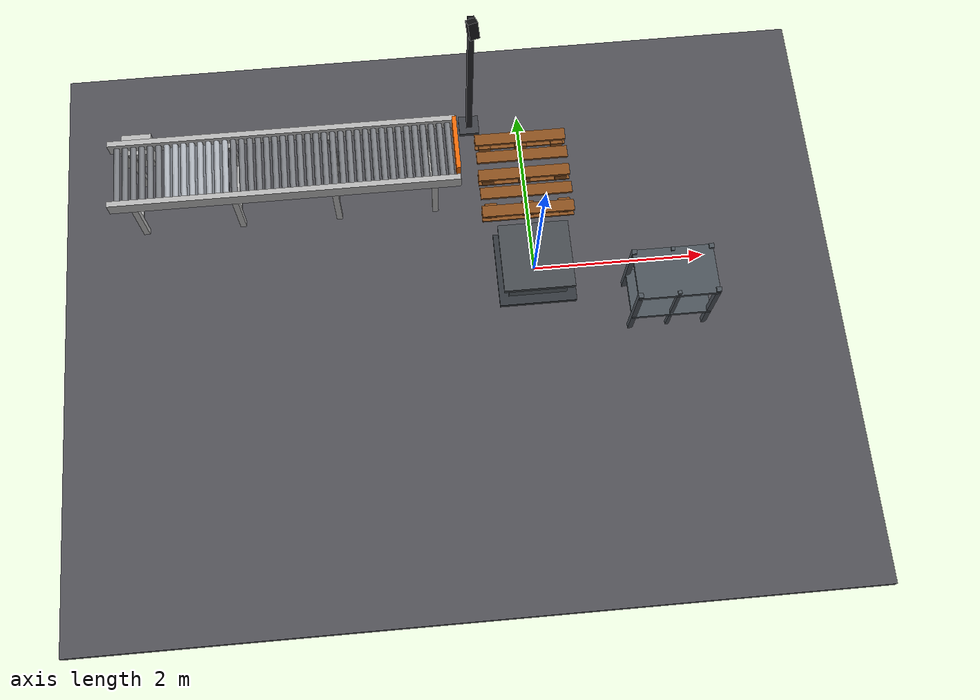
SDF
<?xml version='1.0' encoding='utf-8'?>
<sdf version="1.8">
  <world name="ahead_workcell_v4_2_physical_scale">
    <plugin filename="ignition-gazebo-forcetorque-system" name="gz::sim::systems::ForceTorque" />
    <plugin filename="ignition-gazebo-physics-system" name="ignition::gazebo::systems::Physics" />
    <plugin filename="ignition-gazebo-user-commands-system" name="ignition::gazebo::systems::UserCommands" />
    <plugin filename="ignition-gazebo-contact-system" name="ignition::gazebo::systems::Contact" />
    <plugin filename="ignition-gazebo-scene-broadcaster-system" name="ignition::gazebo::systems::SceneBroadcaster" />
    <plugin filename="ignition-gazebo-sensors-system" name="ignition::gazebo::systems::Sensors">
      <render_engine>ogre2</render_engine>
    </plugin>
    <gravity>0 0 -9.80665</gravity>
    <physics name="default_physics" type="ignored">
      <max_step_size>0.001</max_step_size>
      <real_time_factor>1.0</real_time_factor>
    </physics>
    <light type="directional" name="sun">
      <pose>0 0 8 0 0 0</pose>
      <diffuse>0.8 0.8 0.8 1</diffuse>
      <direction>-0.4 0.3 -1</direction>
    </light>
    <model name="floor">
      <static>true</static>
      <link name="floor_link">
        <collision name="collision">
          <pose>-1.0 -0.5 -0.05 0 0 0</pose>
          <geometry>
            <box>
              <size>9.0 7.0 0.10</size>
            </box>
          </geometry>
        </collision>
        <visual name="visual">
          <pose>-1.0 -0.5 -0.05 0 0 0</pose>
          <geometry>
            <box>
              <size>9.0 7.0 0.10</size>
            </box>
          </geometry>
          <material>
            <ambient>0.22 0.22 0.23 1</ambient>
            <diffuse>0.32 0.32 0.34 1</diffuse>
          </material>
        </visual>
      </link>
    </model>
    <model name="conveyor_main">
      <static>false</static>
      <link name="conveyor_link">
        <inertial>
          <mass>100.0</mass>
          <inertia>
            <ixx>20.0</ixx>
            <iyy>150.0</iyy>
            <izz>150.0</izz>
            <ixy>0</ixy>
            <ixz>0</ixz>
            <iyz>0</iyz>
          </inertia>
        </inertial>
        <visual name="rail_left">
          <pose>-2.80 0.82 0.84 0 0 0</pose>
          <geometry>
            <box>
              <size>4.00 0.065 0.18</size>
            </box>
          </geometry>
        </visual>
        <visual name="rail_right">
          <pose>-2.80 1.58 0.84 0 0 0</pose>
          <geometry>
            <box>
              <size>4.00 0.065 0.18</size>
            </box>
          </geometry>
        </visual>
        <visual name="leg_l_0">
          <pose>-4.55 0.88 0.40 0 0 0</pose>
          <geometry>
            <box>
              <size>0.07 0.07 0.80</size>
            </box>
          </geometry>
        </visual>
        <visual name="leg_r_0">
          <pose>-4.55 1.52 0.40 0 0 0</pose>
          <geometry>
            <box>
              <size>0.07 0.07 0.80</size>
            </box>
          </geometry>
        </visual>
        <visual name="crossbar_0">
          <pose>-4.55 1.20 0.30 0 0 0</pose>
          <geometry>
            <box>
              <size>0.06 0.68 0.06</size>
            </box>
          </geometry>
        </visual>
        <visual name="leg_l_1">
          <pose>-3.4 0.88 0.40 0 0 0</pose>
          <geometry>
            <box>
              <size>0.07 0.07 0.80</size>
            </box>
          </geometry>
        </visual>
        <visual name="leg_r_1">
          <pose>-3.4 1.52 0.40 0 0 0</pose>
          <geometry>
            <box>
              <size>0.07 0.07 0.80</size>
            </box>
          </geometry>
        </visual>
        <visual name="crossbar_1">
          <pose>-3.4 1.20 0.30 0 0 0</pose>
          <geometry>
            <box>
              <size>0.06 0.68 0.06</size>
            </box>
          </geometry>
        </visual>
        <visual name="leg_l_2">
          <pose>-2.25 0.88 0.40 0 0 0</pose>
          <geometry>
            <box>
              <size>0.07 0.07 0.80</size>
            </box>
          </geometry>
        </visual>
        <visual name="leg_r_2">
          <pose>-2.25 1.52 0.40 0 0 0</pose>
          <geometry>
            <box>
              <size>0.07 0.07 0.80</size>
            </box>
          </geometry>
        </visual>
        <visual name="crossbar_2">
          <pose>-2.25 1.20 0.30 0 0 0</pose>
          <geometry>
            <box>
              <size>0.06 0.68 0.06</size>
            </box>
          </geometry>
        </visual>
        <visual name="leg_l_3">
          <pose>-1.1 0.88 0.40 0 0 0</pose>
          <geometry>
            <box>
              <size>0.07 0.07 0.80</size>
            </box>
          </geometry>
        </visual>
        <visual name="leg_r_3">
          <pose>-1.1 1.52 0.40 0 0 0</pose>
          <geometry>
            <box>
              <size>0.07 0.07 0.80</size>
            </box>
          </geometry>
        </visual>
        <visual name="crossbar_3">
          <pose>-1.1 1.20 0.30 0 0 0</pose>
          <geometry>
            <box>
              <size>0.06 0.68 0.06</size>
            </box>
          </geometry>
        </visual>
        <visual name="pick_stopper">
          <pose>-0.82 1.20 0.96 0 0 0</pose>
          <geometry>
            <box>
              <size>0.05 0.66 0.18</size>
            </box>
          </geometry>
          <material>
            <ambient>0.72 0.27 0.02 1</ambient>
            <diffuse>0.95 0.42 0.03 1</diffuse>
          </material>
        </visual>
        <collision name="pick_stopper_collision">
          <pose>-0.82 1.20 0.96 0 0 0</pose>
          <geometry>
            <box>
              <size>0.05 0.66 0.18</size>
            </box>
          </geometry>
          <surface>
            <friction>
              <ode>
                <mu>1.0</mu>
                <mu2>1.0</mu2>
              </ode>
            </friction>
            <contact>
              <ode>
                <kp>1000000</kp>
                <kd>100</kd>
              </ode>
            </contact>
          </surface>
        </collision>
        <visual name="drive_motor">
          <pose>-4.50 1.63 0.63 0 0 0</pose>
          <geometry>
            <box>
              <size>0.34 0.26 0.30</size>
            </box>
          </geometry>
        </visual>
        <collision name="infeed_support_collision">
          <pose>-4.480000 1.200000 0.750000 0 0 0</pose>
          <geometry>
            <box>
              <size>0.540000 0.800000 0.200000</size>
            </box>
          </geometry>
          <surface>
            <friction>
              <ode>
                <mu>0.7</mu>
                <mu2>150</mu2>
                <fdir1>0 1 0</fdir1>
              </ode>
            </friction>
          </surface>
        </collision>
        <collision name="outfeed_support_collision">
          <pose>-2.115000 1.200000 0.750000 0 0 0</pose>
          <geometry>
            <box>
              <size>2.530000 0.800000 0.200000</size>
            </box>
          </geometry>
          <surface>
            <friction>
              <ode>
                <mu>0.7</mu>
                <mu2>150</mu2>
                <fdir1>0 1 0</fdir1>
              </ode>
            </friction>
          </surface>
        </collision>
      </link>
      <joint name="conveyor_world_fixed" type="fixed">
        <parent>world</parent>
        <child>conveyor_link</child>
      </joint>
      <link name="roller_00_link">
        <pose>-4.700000 1.200000 0.860000 0 0 0</pose>
        <inertial>
          <mass>1.0</mass>
          <inertia>
            <ixx>0.03883958</ixx>
            <iyy>0.00061250</iyy>
            <izz>0.03883958</izz>
            <ixy>0</ixy>
            <ixz>0</ixz>
            <iyz>0</iyz>
          </inertia>
        </inertial>
        <visual name="roller_00">
          <pose>0 0 0 1.570796326790 0.000000000000 0.000000000000</pose>
          <geometry>
            <cylinder>
              <radius>0.035</radius>
              <length>0.68</length>
            </cylinder>
          </geometry>
          <material>
            <ambient>0.28 0.29 0.31 1</ambient>
            <diffuse>0.47 0.48 0.50 1</diffuse>
          </material>
        </visual>
        <collision name="roller_00_collision">
          <pose>0 0 0 1.570796326790 0.000000000000 0.000000000000</pose>
          <geometry>
            <cylinder>
              <radius>0.035</radius>
              <length>0.68</length>
            </cylinder>
          </geometry>
          <surface>
            <friction>
              <ode>
                <mu>1.20</mu>
                <mu2>1.20</mu2>
              </ode>
            </friction>
          </surface>
        </collision>
      </link>
      <joint name="roller_00_joint" type="revolute">
        <parent>conveyor_link</parent>
        <child>roller_00_link</child>
        <axis>
          <xyz>0 1 0</xyz>
          <dynamics>
            <damping>0.01</damping>
            <friction>0.0</friction>
          </dynamics>
        </axis>
      </joint>
      <plugin filename="libignition-gazebo-joint-controller-system.so" name="gz::sim::systems::JointController">
        <joint_name>roller_00_joint</joint_name>
        <topic>/pac/conveyor/roller_cmd_vel</topic>
        <initial_velocity>0.0</initial_velocity>
      </plugin>
      <!-- V4.4: intermediate roller (pitch 0.19 -> 0.095 m) so generator SKUs down to 0.22 m stay on >= 2 rollers -->
      <link name="roller_00m_link">
        <pose>-4.605000 1.200000 0.860000 0 0 0</pose>
        <inertial>
          <mass>1.0</mass>
          <inertia>
            <ixx>0.03883958</ixx>
            <iyy>0.00061250</iyy>
            <izz>0.03883958</izz>
            <ixy>0</ixy>
            <ixz>0</ixz>
            <iyz>0</iyz>
          </inertia>
        </inertial>
        <visual name="roller_00m">
          <pose>0 0 0 1.570796326790 0.000000000000 0.000000000000</pose>
          <geometry>
            <cylinder>
              <radius>0.035</radius>
              <length>0.68</length>
            </cylinder>
          </geometry>
          <material>
            <ambient>0.28 0.29 0.31 1</ambient>
            <diffuse>0.47 0.48 0.50 1</diffuse>
          </material>
        </visual>
        <collision name="roller_00m_collision">
          <pose>0 0 0 1.570796326790 0.000000000000 0.000000000000</pose>
          <geometry>
            <cylinder>
              <radius>0.035</radius>
              <length>0.68</length>
            </cylinder>
          </geometry>
          <surface>
            <friction>
              <ode>
                <mu>1.20</mu>
                <mu2>1.20</mu2>
              </ode>
            </friction>
          </surface>
        </collision>
      </link>
      <joint name="roller_00m_joint" type="revolute">
        <parent>conveyor_link</parent>
        <child>roller_00m_link</child>
        <axis>
          <xyz>0 1 0</xyz>
          <dynamics>
            <damping>0.01</damping>
            <friction>0.0</friction>
          </dynamics>
        </axis>
      </joint>
      <plugin filename="libignition-gazebo-joint-controller-system.so" name="gz::sim::systems::JointController">
        <joint_name>roller_00m_joint</joint_name>
        <topic>/pac/conveyor/roller_cmd_vel</topic>
        <initial_velocity>0.0</initial_velocity>
      </plugin>
      <link name="roller_01_link">
        <pose>-4.510000 1.200000 0.860000 0 0 0</pose>
        <inertial>
          <mass>1.0</mass>
          <inertia>
            <ixx>0.03883958</ixx>
            <iyy>0.00061250</iyy>
            <izz>0.03883958</izz>
            <ixy>0</ixy>
            <ixz>0</ixz>
            <iyz>0</iyz>
          </inertia>
        </inertial>
        <visual name="roller_01">
          <pose>0 0 0 1.570796326790 0.000000000000 0.000000000000</pose>
          <geometry>
            <cylinder>
              <radius>0.035</radius>
              <length>0.68</length>
            </cylinder>
          </geometry>
          <material>
            <ambient>0.28 0.29 0.31 1</ambient>
            <diffuse>0.47 0.48 0.50 1</diffuse>
          </material>
        </visual>
        <collision name="roller_01_collision">
          <pose>0 0 0 1.570796326790 0.000000000000 0.000000000000</pose>
          <geometry>
            <cylinder>
              <radius>0.035</radius>
              <length>0.68</length>
            </cylinder>
          </geometry>
          <surface>
            <friction>
              <ode>
                <mu>1.20</mu>
                <mu2>1.20</mu2>
              </ode>
            </friction>
          </surface>
        </collision>
      </link>
      <joint name="roller_01_joint" type="revolute">
        <parent>conveyor_link</parent>
        <child>roller_01_link</child>
        <axis>
          <xyz>0 1 0</xyz>
          <dynamics>
            <damping>0.01</damping>
            <friction>0.0</friction>
          </dynamics>
        </axis>
      </joint>
      <plugin filename="libignition-gazebo-joint-controller-system.so" name="gz::sim::systems::JointController">
        <joint_name>roller_01_joint</joint_name>
        <topic>/pac/conveyor/roller_cmd_vel</topic>
        <initial_velocity>0.0</initial_velocity>
      </plugin>
      <!-- V4.4: intermediate roller (pitch 0.19 -> 0.095 m) so generator SKUs down to 0.22 m stay on >= 2 rollers -->
      <link name="roller_01m_link">
        <pose>-4.415000 1.200000 0.860000 0 0 0</pose>
        <inertial>
          <mass>1.0</mass>
          <inertia>
            <ixx>0.03883958</ixx>
            <iyy>0.00061250</iyy>
            <izz>0.03883958</izz>
            <ixy>0</ixy>
            <ixz>0</ixz>
            <iyz>0</iyz>
          </inertia>
        </inertial>
        <visual name="roller_01m">
          <pose>0 0 0 1.570796326790 0.000000000000 0.000000000000</pose>
          <geometry>
            <cylinder>
              <radius>0.035</radius>
              <length>0.68</length>
            </cylinder>
          </geometry>
          <material>
            <ambient>0.28 0.29 0.31 1</ambient>
            <diffuse>0.47 0.48 0.50 1</diffuse>
          </material>
        </visual>
        <collision name="roller_01m_collision">
          <pose>0 0 0 1.570796326790 0.000000000000 0.000000000000</pose>
          <geometry>
            <cylinder>
              <radius>0.035</radius>
              <length>0.68</length>
            </cylinder>
          </geometry>
          <surface>
            <friction>
              <ode>
                <mu>1.20</mu>
                <mu2>1.20</mu2>
              </ode>
            </friction>
          </surface>
        </collision>
      </link>
      <joint name="roller_01m_joint" type="revolute">
        <parent>conveyor_link</parent>
        <child>roller_01m_link</child>
        <axis>
          <xyz>0 1 0</xyz>
          <dynamics>
            <damping>0.01</damping>
            <friction>0.0</friction>
          </dynamics>
        </axis>
      </joint>
      <plugin filename="libignition-gazebo-joint-controller-system.so" name="gz::sim::systems::JointController">
        <joint_name>roller_01m_joint</joint_name>
        <topic>/pac/conveyor/roller_cmd_vel</topic>
        <initial_velocity>0.0</initial_velocity>
      </plugin>
      <link name="roller_02_link">
        <pose>-4.320000 1.200000 0.860000 0 0 0</pose>
        <inertial>
          <mass>1.0</mass>
          <inertia>
            <ixx>0.03883958</ixx>
            <iyy>0.00061250</iyy>
            <izz>0.03883958</izz>
            <ixy>0</ixy>
            <ixz>0</ixz>
            <iyz>0</iyz>
          </inertia>
        </inertial>
        <visual name="roller_02">
          <pose>0 0 0 1.570796326790 0.000000000000 0.000000000000</pose>
          <geometry>
            <cylinder>
              <radius>0.035</radius>
              <length>0.68</length>
            </cylinder>
          </geometry>
          <material>
            <ambient>0.28 0.29 0.31 1</ambient>
            <diffuse>0.47 0.48 0.50 1</diffuse>
          </material>
        </visual>
        <collision name="roller_02_collision">
          <pose>0 0 0 1.570796326790 0.000000000000 0.000000000000</pose>
          <geometry>
            <cylinder>
              <radius>0.035</radius>
              <length>0.68</length>
            </cylinder>
          </geometry>
          <surface>
            <friction>
              <ode>
                <mu>1.20</mu>
                <mu2>1.20</mu2>
              </ode>
            </friction>
          </surface>
        </collision>
      </link>
      <joint name="roller_02_joint" type="revolute">
        <parent>conveyor_link</parent>
        <child>roller_02_link</child>
        <axis>
          <xyz>0 1 0</xyz>
          <dynamics>
            <damping>0.01</damping>
            <friction>0.0</friction>
          </dynamics>
        </axis>
      </joint>
      <plugin filename="libignition-gazebo-joint-controller-system.so" name="gz::sim::systems::JointController">
        <joint_name>roller_02_joint</joint_name>
        <topic>/pac/conveyor/roller_cmd_vel</topic>
        <initial_velocity>0.0</initial_velocity>
      </plugin>
      <!-- V4.4: intermediate roller (pitch 0.19 -> 0.095 m) so generator SKUs down to 0.22 m stay on >= 2 rollers -->
      <link name="roller_02m_link">
        <pose>-4.225000 1.200000 0.860000 0 0 0</pose>
        <inertial>
          <mass>1.0</mass>
          <inertia>
            <ixx>0.03883958</ixx>
            <iyy>0.00061250</iyy>
            <izz>0.03883958</izz>
            <ixy>0</ixy>
            <ixz>0</ixz>
            <iyz>0</iyz>
          </inertia>
        </inertial>
        <visual name="roller_02m">
          <pose>0 0 0 1.570796326790 0.000000000000 0.000000000000</pose>
          <geometry>
            <cylinder>
              <radius>0.035</radius>
              <length>0.68</length>
            </cylinder>
          </geometry>
          <material>
            <ambient>0.28 0.29 0.31 1</ambient>
            <diffuse>0.47 0.48 0.50 1</diffuse>
          </material>
        </visual>
        <collision name="roller_02m_collision">
          <pose>0 0 0 1.570796326790 0.000000000000 0.000000000000</pose>
          <geometry>
            <cylinder>
              <radius>0.035</radius>
              <length>0.68</length>
            </cylinder>
          </geometry>
          <surface>
            <friction>
              <ode>
                <mu>1.20</mu>
                <mu2>1.20</mu2>
              </ode>
            </friction>
          </surface>
        </collision>
      </link>
      <joint name="roller_02m_joint" type="revolute">
        <parent>conveyor_link</parent>
        <child>roller_02m_link</child>
        <axis>
          <xyz>0 1 0</xyz>
          <dynamics>
            <damping>0.01</damping>
            <friction>0.0</friction>
          </dynamics>
        </axis>
      </joint>
      <plugin filename="libignition-gazebo-joint-controller-system.so" name="gz::sim::systems::JointController">
        <joint_name>roller_02m_joint</joint_name>
        <topic>/pac/conveyor/roller_cmd_vel</topic>
        <initial_velocity>0.0</initial_velocity>
      </plugin>
      <link name="roller_03_link">
        <pose>-4.130000 1.200000 0.860000 0 0 0</pose>
        <inertial>
          <mass>1.0</mass>
          <inertia>
            <ixx>0.03883958</ixx>
            <iyy>0.00061250</iyy>
            <izz>0.03883958</izz>
            <ixy>0</ixy>
            <ixz>0</ixz>
            <iyz>0</iyz>
          </inertia>
        </inertial>
        <visual name="roller_03">
          <pose>0 0 0 1.570796326790 0.000000000000 0.000000000000</pose>
          <geometry>
            <cylinder>
              <radius>0.035</radius>
              <length>0.68</length>
            </cylinder>
          </geometry>
          <material>
            <ambient>0.42 0.44 0.46 1</ambient>
            <diffuse>0.67 0.69 0.72 1</diffuse>
          </material>
        </visual>
        <collision name="roller_03_collision">
          <pose>0 0 0 1.570796326790 0.000000000000 0.000000000000</pose>
          <geometry>
            <cylinder>
              <radius>0.035</radius>
              <length>0.68</length>
            </cylinder>
          </geometry>
          <surface>
            <friction>
              <ode>
                <mu>1.20</mu>
                <mu2>1.20</mu2>
              </ode>
            </friction>
          </surface>
        </collision>
      </link>
      <joint name="roller_03_joint" type="revolute">
        <parent>weigh_platform_link</parent>
        <child>roller_03_link</child>
        <axis>
          <xyz>0 1 0</xyz>
          <dynamics>
            <damping>0.01</damping>
            <friction>0.0</friction>
          </dynamics>
        </axis>
      </joint>
      <plugin filename="libignition-gazebo-joint-controller-system.so" name="gz::sim::systems::JointController">
        <joint_name>roller_03_joint</joint_name>
        <topic>/pac/conveyor/roller_cmd_vel</topic>
        <initial_velocity>0.0</initial_velocity>
      </plugin>
      <!-- V4.4: intermediate roller (pitch 0.19 -> 0.095 m) so generator SKUs down to 0.22 m stay on >= 2 rollers -->
      <link name="roller_03m_link">
        <pose>-4.035000 1.200000 0.860000 0 0 0</pose>
        <inertial>
          <mass>1.0</mass>
          <inertia>
            <ixx>0.03883958</ixx>
            <iyy>0.00061250</iyy>
            <izz>0.03883958</izz>
            <ixy>0</ixy>
            <ixz>0</ixz>
            <iyz>0</iyz>
          </inertia>
        </inertial>
        <visual name="roller_03m">
          <pose>0 0 0 1.570796326790 0.000000000000 0.000000000000</pose>
          <geometry>
            <cylinder>
              <radius>0.035</radius>
              <length>0.68</length>
            </cylinder>
          </geometry>
          <material>
            <ambient>0.42 0.44 0.46 1</ambient>
            <diffuse>0.67 0.69 0.72 1</diffuse>
          </material>
        </visual>
        <collision name="roller_03m_collision">
          <pose>0 0 0 1.570796326790 0.000000000000 0.000000000000</pose>
          <geometry>
            <cylinder>
              <radius>0.035</radius>
              <length>0.68</length>
            </cylinder>
          </geometry>
          <surface>
            <friction>
              <ode>
                <mu>1.20</mu>
                <mu2>1.20</mu2>
              </ode>
            </friction>
          </surface>
        </collision>
      </link>
      <joint name="roller_03m_joint" type="revolute">
        <parent>weigh_platform_link</parent>
        <child>roller_03m_link</child>
        <axis>
          <xyz>0 1 0</xyz>
          <dynamics>
            <damping>0.01</damping>
            <friction>0.0</friction>
          </dynamics>
        </axis>
      </joint>
      <plugin filename="libignition-gazebo-joint-controller-system.so" name="gz::sim::systems::JointController">
        <joint_name>roller_03m_joint</joint_name>
        <topic>/pac/conveyor/roller_cmd_vel</topic>
        <initial_velocity>0.0</initial_velocity>
      </plugin>
      <link name="roller_04_link">
        <pose>-3.940000 1.200000 0.860000 0 0 0</pose>
        <inertial>
          <mass>1.0</mass>
          <inertia>
            <ixx>0.03883958</ixx>
            <iyy>0.00061250</iyy>
            <izz>0.03883958</izz>
            <ixy>0</ixy>
            <ixz>0</ixz>
            <iyz>0</iyz>
          </inertia>
        </inertial>
        <visual name="roller_04">
          <pose>0 0 0 1.570796326790 0.000000000000 0.000000000000</pose>
          <geometry>
            <cylinder>
              <radius>0.035</radius>
              <length>0.68</length>
            </cylinder>
          </geometry>
          <material>
            <ambient>0.42 0.44 0.46 1</ambient>
            <diffuse>0.67 0.69 0.72 1</diffuse>
          </material>
        </visual>
        <collision name="roller_04_collision">
          <pose>0 0 0 1.570796326790 0.000000000000 0.000000000000</pose>
          <geometry>
            <cylinder>
              <radius>0.035</radius>
              <length>0.68</length>
            </cylinder>
          </geometry>
          <surface>
            <friction>
              <ode>
                <mu>1.20</mu>
                <mu2>1.20</mu2>
              </ode>
            </friction>
          </surface>
        </collision>
      </link>
      <joint name="roller_04_joint" type="revolute">
        <parent>weigh_platform_link</parent>
        <child>roller_04_link</child>
        <axis>
          <xyz>0 1 0</xyz>
          <dynamics>
            <damping>0.01</damping>
            <friction>0.0</friction>
          </dynamics>
        </axis>
      </joint>
      <plugin filename="libignition-gazebo-joint-controller-system.so" name="gz::sim::systems::JointController">
        <joint_name>roller_04_joint</joint_name>
        <topic>/pac/conveyor/roller_cmd_vel</topic>
        <initial_velocity>0.0</initial_velocity>
      </plugin>
      <!-- V4.4: intermediate roller (pitch 0.19 -> 0.095 m) so generator SKUs down to 0.22 m stay on >= 2 rollers -->
      <link name="roller_04m_link">
        <pose>-3.845000 1.200000 0.860000 0 0 0</pose>
        <inertial>
          <mass>1.0</mass>
          <inertia>
            <ixx>0.03883958</ixx>
            <iyy>0.00061250</iyy>
            <izz>0.03883958</izz>
            <ixy>0</ixy>
            <ixz>0</ixz>
            <iyz>0</iyz>
          </inertia>
        </inertial>
        <visual name="roller_04m">
          <pose>0 0 0 1.570796326790 0.000000000000 0.000000000000</pose>
          <geometry>
            <cylinder>
              <radius>0.035</radius>
              <length>0.68</length>
            </cylinder>
          </geometry>
          <material>
            <ambient>0.42 0.44 0.46 1</ambient>
            <diffuse>0.67 0.69 0.72 1</diffuse>
          </material>
        </visual>
        <collision name="roller_04m_collision">
          <pose>0 0 0 1.570796326790 0.000000000000 0.000000000000</pose>
          <geometry>
            <cylinder>
              <radius>0.035</radius>
              <length>0.68</length>
            </cylinder>
          </geometry>
          <surface>
            <friction>
              <ode>
                <mu>1.20</mu>
                <mu2>1.20</mu2>
              </ode>
            </friction>
          </surface>
        </collision>
      </link>
      <joint name="roller_04m_joint" type="revolute">
        <parent>weigh_platform_link</parent>
        <child>roller_04m_link</child>
        <axis>
          <xyz>0 1 0</xyz>
          <dynamics>
            <damping>0.01</damping>
            <friction>0.0</friction>
          </dynamics>
        </axis>
      </joint>
      <plugin filename="libignition-gazebo-joint-controller-system.so" name="gz::sim::systems::JointController">
        <joint_name>roller_04m_joint</joint_name>
        <topic>/pac/conveyor/roller_cmd_vel</topic>
        <initial_velocity>0.0</initial_velocity>
      </plugin>
      <link name="roller_05_link">
        <pose>-3.750000 1.200000 0.860000 0 0 0</pose>
        <inertial>
          <mass>1.0</mass>
          <inertia>
            <ixx>0.03883958</ixx>
            <iyy>0.00061250</iyy>
            <izz>0.03883958</izz>
            <ixy>0</ixy>
            <ixz>0</ixz>
            <iyz>0</iyz>
          </inertia>
        </inertial>
        <visual name="roller_05">
          <pose>0 0 0 1.570796326790 0.000000000000 0.000000000000</pose>
          <geometry>
            <cylinder>
              <radius>0.035</radius>
              <length>0.68</length>
            </cylinder>
          </geometry>
          <material>
            <ambient>0.42 0.44 0.46 1</ambient>
            <diffuse>0.67 0.69 0.72 1</diffuse>
          </material>
        </visual>
        <collision name="roller_05_collision">
          <pose>0 0 0 1.570796326790 0.000000000000 0.000000000000</pose>
          <geometry>
            <cylinder>
              <radius>0.035</radius>
              <length>0.68</length>
            </cylinder>
          </geometry>
          <surface>
            <friction>
              <ode>
                <mu>1.20</mu>
                <mu2>1.20</mu2>
              </ode>
            </friction>
          </surface>
        </collision>
      </link>
      <joint name="roller_05_joint" type="revolute">
        <parent>weigh_platform_link</parent>
        <child>roller_05_link</child>
        <axis>
          <xyz>0 1 0</xyz>
          <dynamics>
            <damping>0.01</damping>
            <friction>0.0</friction>
          </dynamics>
        </axis>
      </joint>
      <plugin filename="libignition-gazebo-joint-controller-system.so" name="gz::sim::systems::JointController">
        <joint_name>roller_05_joint</joint_name>
        <topic>/pac/conveyor/roller_cmd_vel</topic>
        <initial_velocity>0.0</initial_velocity>
      </plugin>
      <!-- V4.4: intermediate roller (pitch 0.19 -> 0.095 m) so generator SKUs down to 0.22 m stay on >= 2 rollers -->
      <link name="roller_05m_link">
        <pose>-3.655000 1.200000 0.860000 0 0 0</pose>
        <inertial>
          <mass>1.0</mass>
          <inertia>
            <ixx>0.03883958</ixx>
            <iyy>0.00061250</iyy>
            <izz>0.03883958</izz>
            <ixy>0</ixy>
            <ixz>0</ixz>
            <iyz>0</iyz>
          </inertia>
        </inertial>
        <visual name="roller_05m">
          <pose>0 0 0 1.570796326790 0.000000000000 0.000000000000</pose>
          <geometry>
            <cylinder>
              <radius>0.035</radius>
              <length>0.68</length>
            </cylinder>
          </geometry>
          <material>
            <ambient>0.42 0.44 0.46 1</ambient>
            <diffuse>0.67 0.69 0.72 1</diffuse>
          </material>
        </visual>
        <collision name="roller_05m_collision">
          <pose>0 0 0 1.570796326790 0.000000000000 0.000000000000</pose>
          <geometry>
            <cylinder>
              <radius>0.035</radius>
              <length>0.68</length>
            </cylinder>
          </geometry>
          <surface>
            <friction>
              <ode>
                <mu>1.20</mu>
                <mu2>1.20</mu2>
              </ode>
            </friction>
          </surface>
        </collision>
      </link>
      <joint name="roller_05m_joint" type="revolute">
        <parent>weigh_platform_link</parent>
        <child>roller_05m_link</child>
        <axis>
          <xyz>0 1 0</xyz>
          <dynamics>
            <damping>0.01</damping>
            <friction>0.0</friction>
          </dynamics>
        </axis>
      </joint>
      <plugin filename="libignition-gazebo-joint-controller-system.so" name="gz::sim::systems::JointController">
        <joint_name>roller_05m_joint</joint_name>
        <topic>/pac/conveyor/roller_cmd_vel</topic>
        <initial_velocity>0.0</initial_velocity>
      </plugin>
      <link name="roller_06_link">
        <pose>-3.560000 1.200000 0.860000 0 0 0</pose>
        <inertial>
          <mass>1.0</mass>
          <inertia>
            <ixx>0.03883958</ixx>
            <iyy>0.00061250</iyy>
            <izz>0.03883958</izz>
            <ixy>0</ixy>
            <ixz>0</ixz>
            <iyz>0</iyz>
          </inertia>
        </inertial>
        <visual name="roller_06">
          <pose>0 0 0 1.570796326790 0.000000000000 0.000000000000</pose>
          <geometry>
            <cylinder>
              <radius>0.035</radius>
              <length>0.68</length>
            </cylinder>
          </geometry>
          <material>
            <ambient>0.42 0.44 0.46 1</ambient>
            <diffuse>0.67 0.69 0.72 1</diffuse>
          </material>
        </visual>
        <collision name="roller_06_collision">
          <pose>0 0 0 1.570796326790 0.000000000000 0.000000000000</pose>
          <geometry>
            <cylinder>
              <radius>0.035</radius>
              <length>0.68</length>
            </cylinder>
          </geometry>
          <surface>
            <friction>
              <ode>
                <mu>1.20</mu>
                <mu2>1.20</mu2>
              </ode>
            </friction>
          </surface>
        </collision>
      </link>
      <joint name="roller_06_joint" type="revolute">
        <parent>weigh_platform_link</parent>
        <child>roller_06_link</child>
        <axis>
          <xyz>0 1 0</xyz>
          <dynamics>
            <damping>0.01</damping>
            <friction>0.0</friction>
          </dynamics>
        </axis>
      </joint>
      <plugin filename="libignition-gazebo-joint-controller-system.so" name="gz::sim::systems::JointController">
        <joint_name>roller_06_joint</joint_name>
        <topic>/pac/conveyor/roller_cmd_vel</topic>
        <initial_velocity>0.0</initial_velocity>
      </plugin>
      <!-- V4.4: intermediate roller (pitch 0.19 -> 0.095 m) so generator SKUs down to 0.22 m stay on >= 2 rollers -->
      <link name="roller_06m_link">
        <pose>-3.465000 1.200000 0.860000 0 0 0</pose>
        <inertial>
          <mass>1.0</mass>
          <inertia>
            <ixx>0.03883958</ixx>
            <iyy>0.00061250</iyy>
            <izz>0.03883958</izz>
            <ixy>0</ixy>
            <ixz>0</ixz>
            <iyz>0</iyz>
          </inertia>
        </inertial>
        <visual name="roller_06m">
          <pose>0 0 0 1.570796326790 0.000000000000 0.000000000000</pose>
          <geometry>
            <cylinder>
              <radius>0.035</radius>
              <length>0.68</length>
            </cylinder>
          </geometry>
          <material>
            <ambient>0.42 0.44 0.46 1</ambient>
            <diffuse>0.67 0.69 0.72 1</diffuse>
          </material>
        </visual>
        <collision name="roller_06m_collision">
          <pose>0 0 0 1.570796326790 0.000000000000 0.000000000000</pose>
          <geometry>
            <cylinder>
              <radius>0.035</radius>
              <length>0.68</length>
            </cylinder>
          </geometry>
          <surface>
            <friction>
              <ode>
                <mu>1.20</mu>
                <mu2>1.20</mu2>
              </ode>
            </friction>
          </surface>
        </collision>
      </link>
      <joint name="roller_06m_joint" type="revolute">
        <parent>conveyor_link</parent>
        <child>roller_06m_link</child>
        <axis>
          <xyz>0 1 0</xyz>
          <dynamics>
            <damping>0.01</damping>
            <friction>0.0</friction>
          </dynamics>
        </axis>
      </joint>
      <plugin filename="libignition-gazebo-joint-controller-system.so" name="gz::sim::systems::JointController">
        <joint_name>roller_06m_joint</joint_name>
        <topic>/pac/conveyor/roller_cmd_vel</topic>
        <initial_velocity>0.0</initial_velocity>
      </plugin>
      <link name="roller_07_link">
        <pose>-3.370000 1.200000 0.860000 0 0 0</pose>
        <inertial>
          <mass>1.0</mass>
          <inertia>
            <ixx>0.03883958</ixx>
            <iyy>0.00061250</iyy>
            <izz>0.03883958</izz>
            <ixy>0</ixy>
            <ixz>0</ixz>
            <iyz>0</iyz>
          </inertia>
        </inertial>
        <visual name="roller_07">
          <pose>0 0 0 1.570796326790 0.000000000000 0.000000000000</pose>
          <geometry>
            <cylinder>
              <radius>0.035</radius>
              <length>0.68</length>
            </cylinder>
          </geometry>
          <material>
            <ambient>0.28 0.29 0.31 1</ambient>
            <diffuse>0.47 0.48 0.50 1</diffuse>
          </material>
        </visual>
        <collision name="roller_07_collision">
          <pose>0 0 0 1.570796326790 0.000000000000 0.000000000000</pose>
          <geometry>
            <cylinder>
              <radius>0.035</radius>
              <length>0.68</length>
            </cylinder>
          </geometry>
          <surface>
            <friction>
              <ode>
                <mu>1.20</mu>
                <mu2>1.20</mu2>
              </ode>
            </friction>
          </surface>
        </collision>
      </link>
      <joint name="roller_07_joint" type="revolute">
        <parent>conveyor_link</parent>
        <child>roller_07_link</child>
        <axis>
          <xyz>0 1 0</xyz>
          <dynamics>
            <damping>0.01</damping>
            <friction>0.0</friction>
          </dynamics>
        </axis>
      </joint>
      <plugin filename="libignition-gazebo-joint-controller-system.so" name="gz::sim::systems::JointController">
        <joint_name>roller_07_joint</joint_name>
        <topic>/pac/conveyor/roller_cmd_vel</topic>
        <initial_velocity>0.0</initial_velocity>
      </plugin>
      <!-- V4.4: intermediate roller (pitch 0.19 -> 0.095 m) so generator SKUs down to 0.22 m stay on >= 2 rollers -->
      <link name="roller_07m_link">
        <pose>-3.275000 1.200000 0.860000 0 0 0</pose>
        <inertial>
          <mass>1.0</mass>
          <inertia>
            <ixx>0.03883958</ixx>
            <iyy>0.00061250</iyy>
            <izz>0.03883958</izz>
            <ixy>0</ixy>
            <ixz>0</ixz>
            <iyz>0</iyz>
          </inertia>
        </inertial>
        <visual name="roller_07m">
          <pose>0 0 0 1.570796326790 0.000000000000 0.000000000000</pose>
          <geometry>
            <cylinder>
              <radius>0.035</radius>
              <length>0.68</length>
            </cylinder>
          </geometry>
          <material>
            <ambient>0.28 0.29 0.31 1</ambient>
            <diffuse>0.47 0.48 0.50 1</diffuse>
          </material>
        </visual>
        <collision name="roller_07m_collision">
          <pose>0 0 0 1.570796326790 0.000000000000 0.000000000000</pose>
          <geometry>
            <cylinder>
              <radius>0.035</radius>
              <length>0.68</length>
            </cylinder>
          </geometry>
          <surface>
            <friction>
              <ode>
                <mu>1.20</mu>
                <mu2>1.20</mu2>
              </ode>
            </friction>
          </surface>
        </collision>
      </link>
      <joint name="roller_07m_joint" type="revolute">
        <parent>conveyor_link</parent>
        <child>roller_07m_link</child>
        <axis>
          <xyz>0 1 0</xyz>
          <dynamics>
            <damping>0.01</damping>
            <friction>0.0</friction>
          </dynamics>
        </axis>
      </joint>
      <plugin filename="libignition-gazebo-joint-controller-system.so" name="gz::sim::systems::JointController">
        <joint_name>roller_07m_joint</joint_name>
        <topic>/pac/conveyor/roller_cmd_vel</topic>
        <initial_velocity>0.0</initial_velocity>
      </plugin>
      <link name="roller_08_link">
        <pose>-3.180000 1.200000 0.860000 0 0 0</pose>
        <inertial>
          <mass>1.0</mass>
          <inertia>
            <ixx>0.03883958</ixx>
            <iyy>0.00061250</iyy>
            <izz>0.03883958</izz>
            <ixy>0</ixy>
            <ixz>0</ixz>
            <iyz>0</iyz>
          </inertia>
        </inertial>
        <visual name="roller_08">
          <pose>0 0 0 1.570796326790 0.000000000000 0.000000000000</pose>
          <geometry>
            <cylinder>
              <radius>0.035</radius>
              <length>0.68</length>
            </cylinder>
          </geometry>
          <material>
            <ambient>0.28 0.29 0.31 1</ambient>
            <diffuse>0.47 0.48 0.50 1</diffuse>
          </material>
        </visual>
        <collision name="roller_08_collision">
          <pose>0 0 0 1.570796326790 0.000000000000 0.000000000000</pose>
          <geometry>
            <cylinder>
              <radius>0.035</radius>
              <length>0.68</length>
            </cylinder>
          </geometry>
          <surface>
            <friction>
              <ode>
                <mu>1.20</mu>
                <mu2>1.20</mu2>
              </ode>
            </friction>
          </surface>
        </collision>
      </link>
      <joint name="roller_08_joint" type="revolute">
        <parent>conveyor_link</parent>
        <child>roller_08_link</child>
        <axis>
          <xyz>0 1 0</xyz>
          <dynamics>
            <damping>0.01</damping>
            <friction>0.0</friction>
          </dynamics>
        </axis>
      </joint>
      <plugin filename="libignition-gazebo-joint-controller-system.so" name="gz::sim::systems::JointController">
        <joint_name>roller_08_joint</joint_name>
        <topic>/pac/conveyor/roller_cmd_vel</topic>
        <initial_velocity>0.0</initial_velocity>
      </plugin>
      <!-- V4.4: intermediate roller (pitch 0.19 -> 0.095 m) so generator SKUs down to 0.22 m stay on >= 2 rollers -->
      <link name="roller_08m_link">
        <pose>-3.085000 1.200000 0.860000 0 0 0</pose>
        <inertial>
          <mass>1.0</mass>
          <inertia>
            <ixx>0.03883958</ixx>
            <iyy>0.00061250</iyy>
            <izz>0.03883958</izz>
            <ixy>0</ixy>
            <ixz>0</ixz>
            <iyz>0</iyz>
          </inertia>
        </inertial>
        <visual name="roller_08m">
          <pose>0 0 0 1.570796326790 0.000000000000 0.000000000000</pose>
          <geometry>
            <cylinder>
              <radius>0.035</radius>
              <length>0.68</length>
            </cylinder>
          </geometry>
          <material>
            <ambient>0.28 0.29 0.31 1</ambient>
            <diffuse>0.47 0.48 0.50 1</diffuse>
          </material>
        </visual>
        <collision name="roller_08m_collision">
          <pose>0 0 0 1.570796326790 0.000000000000 0.000000000000</pose>
          <geometry>
            <cylinder>
              <radius>0.035</radius>
              <length>0.68</length>
            </cylinder>
          </geometry>
          <surface>
            <friction>
              <ode>
                <mu>1.20</mu>
                <mu2>1.20</mu2>
              </ode>
            </friction>
          </surface>
        </collision>
      </link>
      <joint name="roller_08m_joint" type="revolute">
        <parent>conveyor_link</parent>
        <child>roller_08m_link</child>
        <axis>
          <xyz>0 1 0</xyz>
          <dynamics>
            <damping>0.01</damping>
            <friction>0.0</friction>
          </dynamics>
        </axis>
      </joint>
      <plugin filename="libignition-gazebo-joint-controller-system.so" name="gz::sim::systems::JointController">
        <joint_name>roller_08m_joint</joint_name>
        <topic>/pac/conveyor/roller_cmd_vel</topic>
        <initial_velocity>0.0</initial_velocity>
      </plugin>
      <link name="roller_09_link">
        <pose>-2.990000 1.200000 0.860000 0 0 0</pose>
        <inertial>
          <mass>1.0</mass>
          <inertia>
            <ixx>0.03883958</ixx>
            <iyy>0.00061250</iyy>
            <izz>0.03883958</izz>
            <ixy>0</ixy>
            <ixz>0</ixz>
            <iyz>0</iyz>
          </inertia>
        </inertial>
        <visual name="roller_09">
          <pose>0 0 0 1.570796326790 0.000000000000 0.000000000000</pose>
          <geometry>
            <cylinder>
              <radius>0.035</radius>
              <length>0.68</length>
            </cylinder>
          </geometry>
          <material>
            <ambient>0.28 0.29 0.31 1</ambient>
            <diffuse>0.47 0.48 0.50 1</diffuse>
          </material>
        </visual>
        <collision name="roller_09_collision">
          <pose>0 0 0 1.570796326790 0.000000000000 0.000000000000</pose>
          <geometry>
            <cylinder>
              <radius>0.035</radius>
              <length>0.68</length>
            </cylinder>
          </geometry>
          <surface>
            <friction>
              <ode>
                <mu>1.20</mu>
                <mu2>1.20</mu2>
              </ode>
            </friction>
          </surface>
        </collision>
      </link>
      <joint name="roller_09_joint" type="revolute">
        <parent>conveyor_link</parent>
        <child>roller_09_link</child>
        <axis>
          <xyz>0 1 0</xyz>
          <dynamics>
            <damping>0.01</damping>
            <friction>0.0</friction>
          </dynamics>
        </axis>
      </joint>
      <plugin filename="libignition-gazebo-joint-controller-system.so" name="gz::sim::systems::JointController">
        <joint_name>roller_09_joint</joint_name>
        <topic>/pac/conveyor/roller_cmd_vel</topic>
        <initial_velocity>0.0</initial_velocity>
      </plugin>
      <!-- V4.4: intermediate roller (pitch 0.19 -> 0.095 m) so generator SKUs down to 0.22 m stay on >= 2 rollers -->
      <link name="roller_09m_link">
        <pose>-2.895000 1.200000 0.860000 0 0 0</pose>
        <inertial>
          <mass>1.0</mass>
          <inertia>
            <ixx>0.03883958</ixx>
            <iyy>0.00061250</iyy>
            <izz>0.03883958</izz>
            <ixy>0</ixy>
            <ixz>0</ixz>
            <iyz>0</iyz>
          </inertia>
        </inertial>
        <visual name="roller_09m">
          <pose>0 0 0 1.570796326790 0.000000000000 0.000000000000</pose>
          <geometry>
            <cylinder>
              <radius>0.035</radius>
              <length>0.68</length>
            </cylinder>
          </geometry>
          <material>
            <ambient>0.28 0.29 0.31 1</ambient>
            <diffuse>0.47 0.48 0.50 1</diffuse>
          </material>
        </visual>
        <collision name="roller_09m_collision">
          <pose>0 0 0 1.570796326790 0.000000000000 0.000000000000</pose>
          <geometry>
            <cylinder>
              <radius>0.035</radius>
              <length>0.68</length>
            </cylinder>
          </geometry>
          <surface>
            <friction>
              <ode>
                <mu>1.20</mu>
                <mu2>1.20</mu2>
              </ode>
            </friction>
          </surface>
        </collision>
      </link>
      <joint name="roller_09m_joint" type="revolute">
        <parent>conveyor_link</parent>
        <child>roller_09m_link</child>
        <axis>
          <xyz>0 1 0</xyz>
          <dynamics>
            <damping>0.01</damping>
            <friction>0.0</friction>
          </dynamics>
        </axis>
      </joint>
      <plugin filename="libignition-gazebo-joint-controller-system.so" name="gz::sim::systems::JointController">
        <joint_name>roller_09m_joint</joint_name>
        <topic>/pac/conveyor/roller_cmd_vel</topic>
        <initial_velocity>0.0</initial_velocity>
      </plugin>
      <link name="roller_10_link">
        <pose>-2.800000 1.200000 0.860000 0 0 0</pose>
        <inertial>
          <mass>1.0</mass>
          <inertia>
            <ixx>0.03883958</ixx>
            <iyy>0.00061250</iyy>
            <izz>0.03883958</izz>
            <ixy>0</ixy>
            <ixz>0</ixz>
            <iyz>0</iyz>
          </inertia>
        </inertial>
        <visual name="roller_10">
          <pose>0 0 0 1.570796326790 0.000000000000 0.000000000000</pose>
          <geometry>
            <cylinder>
              <radius>0.035</radius>
              <length>0.68</length>
            </cylinder>
          </geometry>
          <material>
            <ambient>0.28 0.29 0.31 1</ambient>
            <diffuse>0.47 0.48 0.50 1</diffuse>
          </material>
        </visual>
        <collision name="roller_10_collision">
          <pose>0 0 0 1.570796326790 0.000000000000 0.000000000000</pose>
          <geometry>
            <cylinder>
              <radius>0.035</radius>
              <length>0.68</length>
            </cylinder>
          </geometry>
          <surface>
            <friction>
              <ode>
                <mu>1.20</mu>
                <mu2>1.20</mu2>
              </ode>
            </friction>
          </surface>
        </collision>
      </link>
      <joint name="roller_10_joint" type="revolute">
        <parent>conveyor_link</parent>
        <child>roller_10_link</child>
        <axis>
          <xyz>0 1 0</xyz>
          <dynamics>
            <damping>0.01</damping>
            <friction>0.0</friction>
          </dynamics>
        </axis>
      </joint>
      <plugin filename="libignition-gazebo-joint-controller-system.so" name="gz::sim::systems::JointController">
        <joint_name>roller_10_joint</joint_name>
        <topic>/pac/conveyor/roller_cmd_vel</topic>
        <initial_velocity>0.0</initial_velocity>
      </plugin>
      <!-- V4.4: intermediate roller (pitch 0.19 -> 0.095 m) so generator SKUs down to 0.22 m stay on >= 2 rollers -->
      <link name="roller_10m_link">
        <pose>-2.705000 1.200000 0.860000 0 0 0</pose>
        <inertial>
          <mass>1.0</mass>
          <inertia>
            <ixx>0.03883958</ixx>
            <iyy>0.00061250</iyy>
            <izz>0.03883958</izz>
            <ixy>0</ixy>
            <ixz>0</ixz>
            <iyz>0</iyz>
          </inertia>
        </inertial>
        <visual name="roller_10m">
          <pose>0 0 0 1.570796326790 0.000000000000 0.000000000000</pose>
          <geometry>
            <cylinder>
              <radius>0.035</radius>
              <length>0.68</length>
            </cylinder>
          </geometry>
          <material>
            <ambient>0.28 0.29 0.31 1</ambient>
            <diffuse>0.47 0.48 0.50 1</diffuse>
          </material>
        </visual>
        <collision name="roller_10m_collision">
          <pose>0 0 0 1.570796326790 0.000000000000 0.000000000000</pose>
          <geometry>
            <cylinder>
              <radius>0.035</radius>
              <length>0.68</length>
            </cylinder>
          </geometry>
          <surface>
            <friction>
              <ode>
                <mu>1.20</mu>
                <mu2>1.20</mu2>
              </ode>
            </friction>
          </surface>
        </collision>
      </link>
      <joint name="roller_10m_joint" type="revolute">
        <parent>conveyor_link</parent>
        <child>roller_10m_link</child>
        <axis>
          <xyz>0 1 0</xyz>
          <dynamics>
            <damping>0.01</damping>
            <friction>0.0</friction>
          </dynamics>
        </axis>
      </joint>
      <plugin filename="libignition-gazebo-joint-controller-system.so" name="gz::sim::systems::JointController">
        <joint_name>roller_10m_joint</joint_name>
        <topic>/pac/conveyor/roller_cmd_vel</topic>
        <initial_velocity>0.0</initial_velocity>
      </plugin>
      <link name="roller_11_link">
        <pose>-2.610000 1.200000 0.860000 0 0 0</pose>
        <inertial>
          <mass>1.0</mass>
          <inertia>
            <ixx>0.03883958</ixx>
            <iyy>0.00061250</iyy>
            <izz>0.03883958</izz>
            <ixy>0</ixy>
            <ixz>0</ixz>
            <iyz>0</iyz>
          </inertia>
        </inertial>
        <visual name="roller_11">
          <pose>0 0 0 1.570796326790 0.000000000000 0.000000000000</pose>
          <geometry>
            <cylinder>
              <radius>0.035</radius>
              <length>0.68</length>
            </cylinder>
          </geometry>
          <material>
            <ambient>0.28 0.29 0.31 1</ambient>
            <diffuse>0.47 0.48 0.50 1</diffuse>
          </material>
        </visual>
        <collision name="roller_11_collision">
          <pose>0 0 0 1.570796326790 0.000000000000 0.000000000000</pose>
          <geometry>
            <cylinder>
              <radius>0.035</radius>
              <length>0.68</length>
            </cylinder>
          </geometry>
          <surface>
            <friction>
              <ode>
                <mu>1.20</mu>
                <mu2>1.20</mu2>
              </ode>
            </friction>
          </surface>
        </collision>
      </link>
      <joint name="roller_11_joint" type="revolute">
        <parent>conveyor_link</parent>
        <child>roller_11_link</child>
        <axis>
          <xyz>0 1 0</xyz>
          <dynamics>
            <damping>0.01</damping>
            <friction>0.0</friction>
          </dynamics>
        </axis>
      </joint>
      <plugin filename="libignition-gazebo-joint-controller-system.so" name="gz::sim::systems::JointController">
        <joint_name>roller_11_joint</joint_name>
        <topic>/pac/conveyor/roller_cmd_vel</topic>
        <initial_velocity>0.0</initial_velocity>
      </plugin>
      <!-- V4.4: intermediate roller (pitch 0.19 -> 0.095 m) so generator SKUs down to 0.22 m stay on >= 2 rollers -->
      <link name="roller_11m_link">
        <pose>-2.515000 1.200000 0.860000 0 0 0</pose>
        <inertial>
          <mass>1.0</mass>
          <inertia>
            <ixx>0.03883958</ixx>
            <iyy>0.00061250</iyy>
            <izz>0.03883958</izz>
            <ixy>0</ixy>
            <ixz>0</ixz>
            <iyz>0</iyz>
          </inertia>
        </inertial>
        <visual name="roller_11m">
          <pose>0 0 0 1.570796326790 0.000000000000 0.000000000000</pose>
          <geometry>
            <cylinder>
              <radius>0.035</radius>
              <length>0.68</length>
            </cylinder>
          </geometry>
          <material>
            <ambient>0.28 0.29 0.31 1</ambient>
            <diffuse>0.47 0.48 0.50 1</diffuse>
          </material>
        </visual>
        <collision name="roller_11m_collision">
          <pose>0 0 0 1.570796326790 0.000000000000 0.000000000000</pose>
          <geometry>
            <cylinder>
              <radius>0.035</radius>
              <length>0.68</length>
            </cylinder>
          </geometry>
          <surface>
            <friction>
              <ode>
                <mu>1.20</mu>
                <mu2>1.20</mu2>
              </ode>
            </friction>
          </surface>
        </collision>
      </link>
      <joint name="roller_11m_joint" type="revolute">
        <parent>conveyor_link</parent>
        <child>roller_11m_link</child>
        <axis>
          <xyz>0 1 0</xyz>
          <dynamics>
            <damping>0.01</damping>
            <friction>0.0</friction>
          </dynamics>
        </axis>
      </joint>
      <plugin filename="libignition-gazebo-joint-controller-system.so" name="gz::sim::systems::JointController">
        <joint_name>roller_11m_joint</joint_name>
        <topic>/pac/conveyor/roller_cmd_vel</topic>
        <initial_velocity>0.0</initial_velocity>
      </plugin>
      <link name="roller_12_link">
        <pose>-2.420000 1.200000 0.860000 0 0 0</pose>
        <inertial>
          <mass>1.0</mass>
          <inertia>
            <ixx>0.03883958</ixx>
            <iyy>0.00061250</iyy>
            <izz>0.03883958</izz>
            <ixy>0</ixy>
            <ixz>0</ixz>
            <iyz>0</iyz>
          </inertia>
        </inertial>
        <visual name="roller_12">
          <pose>0 0 0 1.570796326790 0.000000000000 0.000000000000</pose>
          <geometry>
            <cylinder>
              <radius>0.035</radius>
              <length>0.68</length>
            </cylinder>
          </geometry>
          <material>
            <ambient>0.28 0.29 0.31 1</ambient>
            <diffuse>0.47 0.48 0.50 1</diffuse>
          </material>
        </visual>
        <collision name="roller_12_collision">
          <pose>0 0 0 1.570796326790 0.000000000000 0.000000000000</pose>
          <geometry>
            <cylinder>
              <radius>0.035</radius>
              <length>0.68</length>
            </cylinder>
          </geometry>
          <surface>
            <friction>
              <ode>
                <mu>1.20</mu>
                <mu2>1.20</mu2>
              </ode>
            </friction>
          </surface>
        </collision>
      </link>
      <joint name="roller_12_joint" type="revolute">
        <parent>conveyor_link</parent>
        <child>roller_12_link</child>
        <axis>
          <xyz>0 1 0</xyz>
          <dynamics>
            <damping>0.01</damping>
            <friction>0.0</friction>
          </dynamics>
        </axis>
      </joint>
      <plugin filename="libignition-gazebo-joint-controller-system.so" name="gz::sim::systems::JointController">
        <joint_name>roller_12_joint</joint_name>
        <topic>/pac/conveyor/roller_cmd_vel</topic>
        <initial_velocity>0.0</initial_velocity>
      </plugin>
      <!-- V4.4: intermediate roller (pitch 0.19 -> 0.095 m) so generator SKUs down to 0.22 m stay on >= 2 rollers -->
      <link name="roller_12m_link">
        <pose>-2.325000 1.200000 0.860000 0 0 0</pose>
        <inertial>
          <mass>1.0</mass>
          <inertia>
            <ixx>0.03883958</ixx>
            <iyy>0.00061250</iyy>
            <izz>0.03883958</izz>
            <ixy>0</ixy>
            <ixz>0</ixz>
            <iyz>0</iyz>
          </inertia>
        </inertial>
        <visual name="roller_12m">
          <pose>0 0 0 1.570796326790 0.000000000000 0.000000000000</pose>
          <geometry>
            <cylinder>
              <radius>0.035</radius>
              <length>0.68</length>
            </cylinder>
          </geometry>
          <material>
            <ambient>0.28 0.29 0.31 1</ambient>
            <diffuse>0.47 0.48 0.50 1</diffuse>
          </material>
        </visual>
        <collision name="roller_12m_collision">
          <pose>0 0 0 1.570796326790 0.000000000000 0.000000000000</pose>
          <geometry>
            <cylinder>
              <radius>0.035</radius>
              <length>0.68</length>
            </cylinder>
          </geometry>
          <surface>
            <friction>
              <ode>
                <mu>1.20</mu>
                <mu2>1.20</mu2>
              </ode>
            </friction>
          </surface>
        </collision>
      </link>
      <joint name="roller_12m_joint" type="revolute">
        <parent>conveyor_link</parent>
        <child>roller_12m_link</child>
        <axis>
          <xyz>0 1 0</xyz>
          <dynamics>
            <damping>0.01</damping>
            <friction>0.0</friction>
          </dynamics>
        </axis>
      </joint>
      <plugin filename="libignition-gazebo-joint-controller-system.so" name="gz::sim::systems::JointController">
        <joint_name>roller_12m_joint</joint_name>
        <topic>/pac/conveyor/roller_cmd_vel</topic>
        <initial_velocity>0.0</initial_velocity>
      </plugin>
      <link name="roller_13_link">
        <pose>-2.230000 1.200000 0.860000 0 0 0</pose>
        <inertial>
          <mass>1.0</mass>
          <inertia>
            <ixx>0.03883958</ixx>
            <iyy>0.00061250</iyy>
            <izz>0.03883958</izz>
            <ixy>0</ixy>
            <ixz>0</ixz>
            <iyz>0</iyz>
          </inertia>
        </inertial>
        <visual name="roller_13">
          <pose>0 0 0 1.570796326790 0.000000000000 0.000000000000</pose>
          <geometry>
            <cylinder>
              <radius>0.035</radius>
              <length>0.68</length>
            </cylinder>
          </geometry>
          <material>
            <ambient>0.28 0.29 0.31 1</ambient>
            <diffuse>0.47 0.48 0.50 1</diffuse>
          </material>
        </visual>
        <collision name="roller_13_collision">
          <pose>0 0 0 1.570796326790 0.000000000000 0.000000000000</pose>
          <geometry>
            <cylinder>
              <radius>0.035</radius>
              <length>0.68</length>
            </cylinder>
          </geometry>
          <surface>
            <friction>
              <ode>
                <mu>1.20</mu>
                <mu2>1.20</mu2>
              </ode>
            </friction>
          </surface>
        </collision>
      </link>
      <joint name="roller_13_joint" type="revolute">
        <parent>conveyor_link</parent>
        <child>roller_13_link</child>
        <axis>
          <xyz>0 1 0</xyz>
          <dynamics>
            <damping>0.01</damping>
            <friction>0.0</friction>
          </dynamics>
        </axis>
      </joint>
      <plugin filename="libignition-gazebo-joint-controller-system.so" name="gz::sim::systems::JointController">
        <joint_name>roller_13_joint</joint_name>
        <topic>/pac/conveyor/roller_cmd_vel</topic>
        <initial_velocity>0.0</initial_velocity>
      </plugin>
      <!-- V4.4: intermediate roller (pitch 0.19 -> 0.095 m) so generator SKUs down to 0.22 m stay on >= 2 rollers -->
      <link name="roller_13m_link">
        <pose>-2.135000 1.200000 0.860000 0 0 0</pose>
        <inertial>
          <mass>1.0</mass>
          <inertia>
            <ixx>0.03883958</ixx>
            <iyy>0.00061250</iyy>
            <izz>0.03883958</izz>
            <ixy>0</ixy>
            <ixz>0</ixz>
            <iyz>0</iyz>
          </inertia>
        </inertial>
        <visual name="roller_13m">
          <pose>0 0 0 1.570796326790 0.000000000000 0.000000000000</pose>
          <geometry>
            <cylinder>
              <radius>0.035</radius>
              <length>0.68</length>
            </cylinder>
          </geometry>
          <material>
            <ambient>0.28 0.29 0.31 1</ambient>
            <diffuse>0.47 0.48 0.50 1</diffuse>
          </material>
        </visual>
        <collision name="roller_13m_collision">
          <pose>0 0 0 1.570796326790 0.000000000000 0.000000000000</pose>
          <geometry>
            <cylinder>
              <radius>0.035</radius>
              <length>0.68</length>
            </cylinder>
          </geometry>
          <surface>
            <friction>
              <ode>
                <mu>1.20</mu>
                <mu2>1.20</mu2>
              </ode>
            </friction>
          </surface>
        </collision>
      </link>
      <joint name="roller_13m_joint" type="revolute">
        <parent>conveyor_link</parent>
        <child>roller_13m_link</child>
        <axis>
          <xyz>0 1 0</xyz>
          <dynamics>
            <damping>0.01</damping>
            <friction>0.0</friction>
          </dynamics>
        </axis>
      </joint>
      <plugin filename="libignition-gazebo-joint-controller-system.so" name="gz::sim::systems::JointController">
        <joint_name>roller_13m_joint</joint_name>
        <topic>/pac/conveyor/roller_cmd_vel</topic>
        <initial_velocity>0.0</initial_velocity>
      </plugin>
      <link name="roller_14_link">
        <pose>-2.040000 1.200000 0.860000 0 0 0</pose>
        <inertial>
          <mass>1.0</mass>
          <inertia>
            <ixx>0.03883958</ixx>
            <iyy>0.00061250</iyy>
            <izz>0.03883958</izz>
            <ixy>0</ixy>
            <ixz>0</ixz>
            <iyz>0</iyz>
          </inertia>
        </inertial>
        <visual name="roller_14">
          <pose>0 0 0 1.570796326790 0.000000000000 0.000000000000</pose>
          <geometry>
            <cylinder>
              <radius>0.035</radius>
              <length>0.68</length>
            </cylinder>
          </geometry>
          <material>
            <ambient>0.28 0.29 0.31 1</ambient>
            <diffuse>0.47 0.48 0.50 1</diffuse>
          </material>
        </visual>
        <collision name="roller_14_collision">
          <pose>0 0 0 1.570796326790 0.000000000000 0.000000000000</pose>
          <geometry>
            <cylinder>
              <radius>0.035</radius>
              <length>0.68</length>
            </cylinder>
          </geometry>
          <surface>
            <friction>
              <ode>
                <mu>1.20</mu>
                <mu2>1.20</mu2>
              </ode>
            </friction>
          </surface>
        </collision>
      </link>
      <joint name="roller_14_joint" type="revolute">
        <parent>conveyor_link</parent>
        <child>roller_14_link</child>
        <axis>
          <xyz>0 1 0</xyz>
          <dynamics>
            <damping>0.01</damping>
            <friction>0.0</friction>
          </dynamics>
        </axis>
      </joint>
      <plugin filename="libignition-gazebo-joint-controller-system.so" name="gz::sim::systems::JointController">
        <joint_name>roller_14_joint</joint_name>
        <topic>/pac/conveyor/roller_cmd_vel</topic>
        <initial_velocity>0.0</initial_velocity>
      </plugin>
      <!-- V4.4: intermediate roller (pitch 0.19 -> 0.095 m) so generator SKUs down to 0.22 m stay on >= 2 rollers -->
      <link name="roller_14m_link">
        <pose>-1.945000 1.200000 0.860000 0 0 0</pose>
        <inertial>
          <mass>1.0</mass>
          <inertia>
            <ixx>0.03883958</ixx>
            <iyy>0.00061250</iyy>
            <izz>0.03883958</izz>
            <ixy>0</ixy>
            <ixz>0</ixz>
            <iyz>0</iyz>
          </inertia>
        </inertial>
        <visual name="roller_14m">
          <pose>0 0 0 1.570796326790 0.000000000000 0.000000000000</pose>
          <geometry>
            <cylinder>
              <radius>0.035</radius>
              <length>0.68</length>
            </cylinder>
          </geometry>
          <material>
            <ambient>0.28 0.29 0.31 1</ambient>
            <diffuse>0.47 0.48 0.50 1</diffuse>
          </material>
        </visual>
        <collision name="roller_14m_collision">
          <pose>0 0 0 1.570796326790 0.000000000000 0.000000000000</pose>
          <geometry>
            <cylinder>
              <radius>0.035</radius>
              <length>0.68</length>
            </cylinder>
          </geometry>
          <surface>
            <friction>
              <ode>
                <mu>1.20</mu>
                <mu2>1.20</mu2>
              </ode>
            </friction>
          </surface>
        </collision>
      </link>
      <joint name="roller_14m_joint" type="revolute">
        <parent>conveyor_link</parent>
        <child>roller_14m_link</child>
        <axis>
          <xyz>0 1 0</xyz>
          <dynamics>
            <damping>0.01</damping>
            <friction>0.0</friction>
          </dynamics>
        </axis>
      </joint>
      <plugin filename="libignition-gazebo-joint-controller-system.so" name="gz::sim::systems::JointController">
        <joint_name>roller_14m_joint</joint_name>
        <topic>/pac/conveyor/roller_cmd_vel</topic>
        <initial_velocity>0.0</initial_velocity>
      </plugin>
      <link name="roller_15_link">
        <pose>-1.850000 1.200000 0.860000 0 0 0</pose>
        <inertial>
          <mass>1.0</mass>
          <inertia>
            <ixx>0.03883958</ixx>
            <iyy>0.00061250</iyy>
            <izz>0.03883958</izz>
            <ixy>0</ixy>
            <ixz>0</ixz>
            <iyz>0</iyz>
          </inertia>
        </inertial>
        <visual name="roller_15">
          <pose>0 0 0 1.570796326790 0.000000000000 0.000000000000</pose>
          <geometry>
            <cylinder>
              <radius>0.035</radius>
              <length>0.68</length>
            </cylinder>
          </geometry>
          <material>
            <ambient>0.28 0.29 0.31 1</ambient>
            <diffuse>0.47 0.48 0.50 1</diffuse>
          </material>
        </visual>
        <collision name="roller_15_collision">
          <pose>0 0 0 1.570796326790 0.000000000000 0.000000000000</pose>
          <geometry>
            <cylinder>
              <radius>0.035</radius>
              <length>0.68</length>
            </cylinder>
          </geometry>
          <surface>
            <friction>
              <ode>
                <mu>1.20</mu>
                <mu2>1.20</mu2>
              </ode>
            </friction>
          </surface>
        </collision>
      </link>
      <joint name="roller_15_joint" type="revolute">
        <parent>conveyor_link</parent>
        <child>roller_15_link</child>
        <axis>
          <xyz>0 1 0</xyz>
          <dynamics>
            <damping>0.01</damping>
            <friction>0.0</friction>
          </dynamics>
        </axis>
      </joint>
      <plugin filename="libignition-gazebo-joint-controller-system.so" name="gz::sim::systems::JointController">
        <joint_name>roller_15_joint</joint_name>
        <topic>/pac/conveyor/roller_cmd_vel</topic>
        <initial_velocity>0.0</initial_velocity>
      </plugin>
      <!-- V4.4: intermediate roller (pitch 0.19 -> 0.095 m) so generator SKUs down to 0.22 m stay on >= 2 rollers -->
      <link name="roller_15m_link">
        <pose>-1.755000 1.200000 0.860000 0 0 0</pose>
        <inertial>
          <mass>1.0</mass>
          <inertia>
            <ixx>0.03883958</ixx>
            <iyy>0.00061250</iyy>
            <izz>0.03883958</izz>
            <ixy>0</ixy>
            <ixz>0</ixz>
            <iyz>0</iyz>
          </inertia>
        </inertial>
        <visual name="roller_15m">
          <pose>0 0 0 1.570796326790 0.000000000000 0.000000000000</pose>
          <geometry>
            <cylinder>
              <radius>0.035</radius>
              <length>0.68</length>
            </cylinder>
          </geometry>
          <material>
            <ambient>0.28 0.29 0.31 1</ambient>
            <diffuse>0.47 0.48 0.50 1</diffuse>
          </material>
        </visual>
        <collision name="roller_15m_collision">
          <pose>0 0 0 1.570796326790 0.000000000000 0.000000000000</pose>
          <geometry>
            <cylinder>
              <radius>0.035</radius>
              <length>0.68</length>
            </cylinder>
          </geometry>
          <surface>
            <friction>
              <ode>
                <mu>1.20</mu>
                <mu2>1.20</mu2>
              </ode>
            </friction>
          </surface>
        </collision>
      </link>
      <joint name="roller_15m_joint" type="revolute">
        <parent>conveyor_link</parent>
        <child>roller_15m_link</child>
        <axis>
          <xyz>0 1 0</xyz>
          <dynamics>
            <damping>0.01</damping>
            <friction>0.0</friction>
          </dynamics>
        </axis>
      </joint>
      <plugin filename="libignition-gazebo-joint-controller-system.so" name="gz::sim::systems::JointController">
        <joint_name>roller_15m_joint</joint_name>
        <topic>/pac/conveyor/roller_cmd_vel</topic>
        <initial_velocity>0.0</initial_velocity>
      </plugin>
      <link name="roller_16_link">
        <pose>-1.660000 1.200000 0.860000 0 0 0</pose>
        <inertial>
          <mass>1.0</mass>
          <inertia>
            <ixx>0.03883958</ixx>
            <iyy>0.00061250</iyy>
            <izz>0.03883958</izz>
            <ixy>0</ixy>
            <ixz>0</ixz>
            <iyz>0</iyz>
          </inertia>
        </inertial>
        <visual name="roller_16">
          <pose>0 0 0 1.570796326790 0.000000000000 0.000000000000</pose>
          <geometry>
            <cylinder>
              <radius>0.035</radius>
              <length>0.68</length>
            </cylinder>
          </geometry>
          <material>
            <ambient>0.28 0.29 0.31 1</ambient>
            <diffuse>0.47 0.48 0.50 1</diffuse>
          </material>
        </visual>
        <collision name="roller_16_collision">
          <pose>0 0 0 1.570796326790 0.000000000000 0.000000000000</pose>
          <geometry>
            <cylinder>
              <radius>0.035</radius>
              <length>0.68</length>
            </cylinder>
          </geometry>
          <surface>
            <friction>
              <ode>
                <mu>1.20</mu>
                <mu2>1.20</mu2>
              </ode>
            </friction>
          </surface>
        </collision>
      </link>
      <joint name="roller_16_joint" type="revolute">
        <parent>conveyor_link</parent>
        <child>roller_16_link</child>
        <axis>
          <xyz>0 1 0</xyz>
          <dynamics>
            <damping>0.01</damping>
            <friction>0.0</friction>
          </dynamics>
        </axis>
      </joint>
      <plugin filename="libignition-gazebo-joint-controller-system.so" name="gz::sim::systems::JointController">
        <joint_name>roller_16_joint</joint_name>
        <topic>/pac/conveyor/roller_cmd_vel</topic>
        <initial_velocity>0.0</initial_velocity>
      </plugin>
      <!-- V4.4: intermediate roller (pitch 0.19 -> 0.095 m) so generator SKUs down to 0.22 m stay on >= 2 rollers -->
      <link name="roller_16m_link">
        <pose>-1.565000 1.200000 0.860000 0 0 0</pose>
        <inertial>
          <mass>1.0</mass>
          <inertia>
            <ixx>0.03883958</ixx>
            <iyy>0.00061250</iyy>
            <izz>0.03883958</izz>
            <ixy>0</ixy>
            <ixz>0</ixz>
            <iyz>0</iyz>
          </inertia>
        </inertial>
        <visual name="roller_16m">
          <pose>0 0 0 1.570796326790 0.000000000000 0.000000000000</pose>
          <geometry>
            <cylinder>
              <radius>0.035</radius>
              <length>0.68</length>
            </cylinder>
          </geometry>
          <material>
            <ambient>0.28 0.29 0.31 1</ambient>
            <diffuse>0.47 0.48 0.50 1</diffuse>
          </material>
        </visual>
        <collision name="roller_16m_collision">
          <pose>0 0 0 1.570796326790 0.000000000000 0.000000000000</pose>
          <geometry>
            <cylinder>
              <radius>0.035</radius>
              <length>0.68</length>
            </cylinder>
          </geometry>
          <surface>
            <friction>
              <ode>
                <mu>1.20</mu>
                <mu2>1.20</mu2>
              </ode>
            </friction>
          </surface>
        </collision>
      </link>
      <joint name="roller_16m_joint" type="revolute">
        <parent>conveyor_link</parent>
        <child>roller_16m_link</child>
        <axis>
          <xyz>0 1 0</xyz>
          <dynamics>
            <damping>0.01</damping>
            <friction>0.0</friction>
          </dynamics>
        </axis>
      </joint>
      <plugin filename="libignition-gazebo-joint-controller-system.so" name="gz::sim::systems::JointController">
        <joint_name>roller_16m_joint</joint_name>
        <topic>/pac/conveyor/roller_cmd_vel</topic>
        <initial_velocity>0.0</initial_velocity>
      </plugin>
      <link name="roller_17_link">
        <pose>-1.470000 1.200000 0.860000 0 0 0</pose>
        <inertial>
          <mass>1.0</mass>
          <inertia>
            <ixx>0.03883958</ixx>
            <iyy>0.00061250</iyy>
            <izz>0.03883958</izz>
            <ixy>0</ixy>
            <ixz>0</ixz>
            <iyz>0</iyz>
          </inertia>
        </inertial>
        <visual name="roller_17">
          <pose>0 0 0 1.570796326790 0.000000000000 0.000000000000</pose>
          <geometry>
            <cylinder>
              <radius>0.035</radius>
              <length>0.68</length>
            </cylinder>
          </geometry>
          <material>
            <ambient>0.28 0.29 0.31 1</ambient>
            <diffuse>0.47 0.48 0.50 1</diffuse>
          </material>
        </visual>
        <collision name="roller_17_collision">
          <pose>0 0 0 1.570796326790 0.000000000000 0.000000000000</pose>
          <geometry>
            <cylinder>
              <radius>0.035</radius>
              <length>0.68</length>
            </cylinder>
          </geometry>
          <surface>
            <friction>
              <ode>
                <mu>1.20</mu>
                <mu2>1.20</mu2>
              </ode>
            </friction>
          </surface>
        </collision>
      </link>
      <joint name="roller_17_joint" type="revolute">
        <parent>conveyor_link</parent>
        <child>roller_17_link</child>
        <axis>
          <xyz>0 1 0</xyz>
          <dynamics>
            <damping>0.01</damping>
            <friction>0.0</friction>
          </dynamics>
        </axis>
      </joint>
      <plugin filename="libignition-gazebo-joint-controller-system.so" name="gz::sim::systems::JointController">
        <joint_name>roller_17_joint</joint_name>
        <topic>/pac/conveyor/roller_cmd_vel</topic>
        <initial_velocity>0.0</initial_velocity>
      </plugin>
      <!-- V4.4: intermediate roller (pitch 0.19 -> 0.095 m) so generator SKUs down to 0.22 m stay on >= 2 rollers -->
      <link name="roller_17m_link">
        <pose>-1.375000 1.200000 0.860000 0 0 0</pose>
        <inertial>
          <mass>1.0</mass>
          <inertia>
            <ixx>0.03883958</ixx>
            <iyy>0.00061250</iyy>
            <izz>0.03883958</izz>
            <ixy>0</ixy>
            <ixz>0</ixz>
            <iyz>0</iyz>
          </inertia>
        </inertial>
        <visual name="roller_17m">
          <pose>0 0 0 1.570796326790 0.000000000000 0.000000000000</pose>
          <geometry>
            <cylinder>
              <radius>0.035</radius>
              <length>0.68</length>
            </cylinder>
          </geometry>
          <material>
            <ambient>0.28 0.29 0.31 1</ambient>
            <diffuse>0.47 0.48 0.50 1</diffuse>
          </material>
        </visual>
        <collision name="roller_17m_collision">
          <pose>0 0 0 1.570796326790 0.000000000000 0.000000000000</pose>
          <geometry>
            <cylinder>
              <radius>0.035</radius>
              <length>0.68</length>
            </cylinder>
          </geometry>
          <surface>
            <friction>
              <ode>
                <mu>1.20</mu>
                <mu2>1.20</mu2>
              </ode>
            </friction>
          </surface>
        </collision>
      </link>
      <joint name="roller_17m_joint" type="revolute">
        <parent>conveyor_link</parent>
        <child>roller_17m_link</child>
        <axis>
          <xyz>0 1 0</xyz>
          <dynamics>
            <damping>0.01</damping>
            <friction>0.0</friction>
          </dynamics>
        </axis>
      </joint>
      <plugin filename="libignition-gazebo-joint-controller-system.so" name="gz::sim::systems::JointController">
        <joint_name>roller_17m_joint</joint_name>
        <topic>/pac/conveyor/roller_cmd_vel</topic>
        <initial_velocity>0.0</initial_velocity>
      </plugin>
      <link name="roller_18_link">
        <pose>-1.280000 1.200000 0.860000 0 0 0</pose>
        <inertial>
          <mass>1.0</mass>
          <inertia>
            <ixx>0.03883958</ixx>
            <iyy>0.00061250</iyy>
            <izz>0.03883958</izz>
            <ixy>0</ixy>
            <ixz>0</ixz>
            <iyz>0</iyz>
          </inertia>
        </inertial>
        <visual name="roller_18">
          <pose>0 0 0 1.570796326790 0.000000000000 0.000000000000</pose>
          <geometry>
            <cylinder>
              <radius>0.035</radius>
              <length>0.68</length>
            </cylinder>
          </geometry>
          <material>
            <ambient>0.28 0.29 0.31 1</ambient>
            <diffuse>0.47 0.48 0.50 1</diffuse>
          </material>
        </visual>
        <collision name="roller_18_collision">
          <pose>0 0 0 1.570796326790 0.000000000000 0.000000000000</pose>
          <geometry>
            <cylinder>
              <radius>0.035</radius>
              <length>0.68</length>
            </cylinder>
          </geometry>
          <surface>
            <friction>
              <ode>
                <mu>1.20</mu>
                <mu2>1.20</mu2>
              </ode>
            </friction>
          </surface>
        </collision>
      </link>
      <joint name="roller_18_joint" type="revolute">
        <parent>conveyor_link</parent>
        <child>roller_18_link</child>
        <axis>
          <xyz>0 1 0</xyz>
          <dynamics>
            <damping>0.01</damping>
            <friction>0.0</friction>
          </dynamics>
        </axis>
      </joint>
      <plugin filename="libignition-gazebo-joint-controller-system.so" name="gz::sim::systems::JointController">
        <joint_name>roller_18_joint</joint_name>
        <topic>/pac/conveyor/roller_cmd_vel</topic>
        <initial_velocity>0.0</initial_velocity>
      </plugin>
      <!-- V4.4: intermediate roller (pitch 0.19 -> 0.095 m) so generator SKUs down to 0.22 m stay on >= 2 rollers -->
      <link name="roller_18m_link">
        <pose>-1.185000 1.200000 0.860000 0 0 0</pose>
        <inertial>
          <mass>1.0</mass>
          <inertia>
            <ixx>0.03883958</ixx>
            <iyy>0.00061250</iyy>
            <izz>0.03883958</izz>
            <ixy>0</ixy>
            <ixz>0</ixz>
            <iyz>0</iyz>
          </inertia>
        </inertial>
        <visual name="roller_18m">
          <pose>0 0 0 1.570796326790 0.000000000000 0.000000000000</pose>
          <geometry>
            <cylinder>
              <radius>0.035</radius>
              <length>0.68</length>
            </cylinder>
          </geometry>
          <material>
            <ambient>0.28 0.29 0.31 1</ambient>
            <diffuse>0.47 0.48 0.50 1</diffuse>
          </material>
        </visual>
        <collision name="roller_18m_collision">
          <pose>0 0 0 1.570796326790 0.000000000000 0.000000000000</pose>
          <geometry>
            <cylinder>
              <radius>0.035</radius>
              <length>0.68</length>
            </cylinder>
          </geometry>
          <surface>
            <friction>
              <ode>
                <mu>1.20</mu>
                <mu2>1.20</mu2>
              </ode>
            </friction>
          </surface>
        </collision>
      </link>
      <joint name="roller_18m_joint" type="revolute">
        <parent>conveyor_link</parent>
        <child>roller_18m_link</child>
        <axis>
          <xyz>0 1 0</xyz>
          <dynamics>
            <damping>0.01</damping>
            <friction>0.0</friction>
          </dynamics>
        </axis>
      </joint>
      <plugin filename="libignition-gazebo-joint-controller-system.so" name="gz::sim::systems::JointController">
        <joint_name>roller_18m_joint</joint_name>
        <topic>/pac/conveyor/roller_cmd_vel</topic>
        <initial_velocity>0.0</initial_velocity>
      </plugin>
      <link name="roller_19_link">
        <pose>-1.090000 1.200000 0.860000 0 0 0</pose>
        <inertial>
          <mass>1.0</mass>
          <inertia>
            <ixx>0.03883958</ixx>
            <iyy>0.00061250</iyy>
            <izz>0.03883958</izz>
            <ixy>0</ixy>
            <ixz>0</ixz>
            <iyz>0</iyz>
          </inertia>
        </inertial>
        <visual name="roller_19">
          <pose>0 0 0 1.570796326790 0.000000000000 0.000000000000</pose>
          <geometry>
            <cylinder>
              <radius>0.035</radius>
              <length>0.68</length>
            </cylinder>
          </geometry>
          <material>
            <ambient>0.28 0.29 0.31 1</ambient>
            <diffuse>0.47 0.48 0.50 1</diffuse>
          </material>
        </visual>
        <collision name="roller_19_collision">
          <pose>0 0 0 1.570796326790 0.000000000000 0.000000000000</pose>
          <geometry>
            <cylinder>
              <radius>0.035</radius>
              <length>0.68</length>
            </cylinder>
          </geometry>
          <surface>
            <friction>
              <ode>
                <mu>1.20</mu>
                <mu2>1.20</mu2>
              </ode>
            </friction>
          </surface>
        </collision>
      </link>
      <joint name="roller_19_joint" type="revolute">
        <parent>conveyor_link</parent>
        <child>roller_19_link</child>
        <axis>
          <xyz>0 1 0</xyz>
          <dynamics>
            <damping>0.01</damping>
            <friction>0.0</friction>
          </dynamics>
        </axis>
      </joint>
      <plugin filename="libignition-gazebo-joint-controller-system.so" name="gz::sim::systems::JointController">
        <joint_name>roller_19_joint</joint_name>
        <topic>/pac/conveyor/roller_cmd_vel</topic>
        <initial_velocity>0.0</initial_velocity>
      </plugin>
      <!-- V4.4: intermediate roller (pitch 0.19 -> 0.095 m) so generator SKUs down to 0.22 m stay on >= 2 rollers -->
      <link name="roller_19m_link">
        <pose>-0.995000 1.200000 0.860000 0 0 0</pose>
        <inertial>
          <mass>1.0</mass>
          <inertia>
            <ixx>0.03883958</ixx>
            <iyy>0.00061250</iyy>
            <izz>0.03883958</izz>
            <ixy>0</ixy>
            <ixz>0</ixz>
            <iyz>0</iyz>
          </inertia>
        </inertial>
        <visual name="roller_19m">
          <pose>0 0 0 1.570796326790 0.000000000000 0.000000000000</pose>
          <geometry>
            <cylinder>
              <radius>0.035</radius>
              <length>0.68</length>
            </cylinder>
          </geometry>
          <material>
            <ambient>0.28 0.29 0.31 1</ambient>
            <diffuse>0.47 0.48 0.50 1</diffuse>
          </material>
        </visual>
        <collision name="roller_19m_collision">
          <pose>0 0 0 1.570796326790 0.000000000000 0.000000000000</pose>
          <geometry>
            <cylinder>
              <radius>0.035</radius>
              <length>0.68</length>
            </cylinder>
          </geometry>
          <surface>
            <friction>
              <ode>
                <mu>1.20</mu>
                <mu2>1.20</mu2>
              </ode>
            </friction>
          </surface>
        </collision>
      </link>
      <joint name="roller_19m_joint" type="revolute">
        <parent>conveyor_link</parent>
        <child>roller_19m_link</child>
        <axis>
          <xyz>0 1 0</xyz>
          <dynamics>
            <damping>0.01</damping>
            <friction>0.0</friction>
          </dynamics>
        </axis>
      </joint>
      <plugin filename="libignition-gazebo-joint-controller-system.so" name="gz::sim::systems::JointController">
        <joint_name>roller_19m_joint</joint_name>
        <topic>/pac/conveyor/roller_cmd_vel</topic>
        <initial_velocity>0.0</initial_velocity>
      </plugin>
      <link name="roller_20_link">
        <pose>-0.900000 1.200000 0.860000 0 0 0</pose>
        <inertial>
          <mass>1.0</mass>
          <inertia>
            <ixx>0.03883958</ixx>
            <iyy>0.00061250</iyy>
            <izz>0.03883958</izz>
            <ixy>0</ixy>
            <ixz>0</ixz>
            <iyz>0</iyz>
          </inertia>
        </inertial>
        <visual name="roller_20">
          <pose>0 0 0 1.570796326790 0.000000000000 0.000000000000</pose>
          <geometry>
            <cylinder>
              <radius>0.035</radius>
              <length>0.68</length>
            </cylinder>
          </geometry>
          <material>
            <ambient>0.28 0.29 0.31 1</ambient>
            <diffuse>0.47 0.48 0.50 1</diffuse>
          </material>
        </visual>
        <collision name="roller_20_collision">
          <pose>0 0 0 1.570796326790 0.000000000000 0.000000000000</pose>
          <geometry>
            <cylinder>
              <radius>0.035</radius>
              <length>0.68</length>
            </cylinder>
          </geometry>
          <surface>
            <friction>
              <ode>
                <mu>1.20</mu>
                <mu2>1.20</mu2>
              </ode>
            </friction>
          </surface>
        </collision>
      </link>
      <joint name="roller_20_joint" type="revolute">
        <parent>conveyor_link</parent>
        <child>roller_20_link</child>
        <axis>
          <xyz>0 1 0</xyz>
          <dynamics>
            <damping>0.01</damping>
            <friction>0.0</friction>
          </dynamics>
        </axis>
      </joint>
      <plugin filename="libignition-gazebo-joint-controller-system.so" name="gz::sim::systems::JointController">
        <joint_name>roller_20_joint</joint_name>
        <topic>/pac/conveyor/roller_cmd_vel</topic>
        <initial_velocity>0.0</initial_velocity>
      </plugin>
      <link name="weigh_platform_link">
        <pose>-3.80 1.20 0.755 0 0 0</pose>
        <inertial>
          <mass>3.0</mass>
          <inertia>
            <ixx>0.1243</ixx>
            <iyy>0.1243</iyy>
            <izz>0.2450</izz>
            <ixy>0</ixy>
            <ixz>0</ixz>
            <iyz>0</iyz>
          </inertia>
        </inertial>
        <collision name="scale_platform_collision">
          <geometry>
            <box>
              <size>0.70 0.70 0.085</size>
            </box>
          </geometry>
        </collision>
      </link>
      <joint name="scale_loadcell_joint" type="fixed">
        <parent>conveyor_link</parent>
        <child>weigh_platform_link</child>
        <sensor name="scale_force_torque" type="force_torque">
          <always_on>true</always_on>
          <update_rate>100</update_rate>
          <topic>/pac/scale/wrench</topic>
          <force_torque>
            <frame>child</frame>
            <measure_direction>parent_to_child</measure_direction>
          </force_torque>
        </sensor>
      </joint>
    </model>
    <model name="inline_scale">
      <static>true</static>
      <link name="scale_link">
        <visual name="weighing_frame">
          <pose>-3.80 1.20 0.755 0 0 0</pose>
          <geometry>
            <box>
              <size>0.70 0.70 0.085</size>
            </box>
          </geometry>
          <material>
            <ambient>0.25 0.26 0.28 1</ambient>
            <diffuse>0.48 0.50 0.53 1</diffuse>
          </material>
        </visual>
        <visual name="loadcell_base">
          <pose>-3.80 1.20 0.685 0 0 0</pose>
          <geometry>
            <box>
              <size>0.56 0.54 0.045</size>
            </box>
          </geometry>
        </visual>
      </link>
    </model>
    <model name="hdr50_pedestal">
      <static>true</static>
      <pose>0 0 0 0 0 0</pose>
      <link name="pedestal_link">
        <collision name="base_plate_collision">
          <pose>0 0 0.025 0 0 0</pose>
          <geometry>
            <box>
              <size>0.90 0.90 0.05</size>
            </box>
          </geometry>
        </collision>
        <visual name="base_plate_visual">
          <pose>0 0 0.025 0 0 0</pose>
          <geometry>
            <box>
              <size>0.90 0.90 0.05</size>
            </box>
          </geometry>
          <material>
            <ambient>0.10 0.11 0.12 1</ambient>
            <diffuse>0.20 0.22 0.24 1</diffuse>
          </material>
        </visual>
        <collision name="column_collision">
          <pose>0 0 0.205 0 0 0</pose>
          <geometry>
            <box>
              <size>0.68 0.68 0.31</size>
            </box>
          </geometry>
        </collision>
        <visual name="column_visual">
          <pose>0 0 0.205 0 0 0</pose>
          <geometry>
            <box>
              <size>0.68 0.68 0.31</size>
            </box>
          </geometry>
          <material>
            <ambient>0.18 0.20 0.22 1</ambient>
            <diffuse>0.34 0.37 0.40 1</diffuse>
          </material>
        </visual>
        <collision name="top_plate_collision">
          <pose>0 0 0.375 0 0 0</pose>
          <geometry>
            <box>
              <size>0.82 0.82 0.05</size>
            </box>
          </geometry>
        </collision>
        <visual name="top_plate_visual">
          <pose>0 0 0.375 0 0 0</pose>
          <geometry>
            <box>
              <size>0.82 0.82 0.05</size>
            </box>
          </geometry>
          <material>
            <ambient>0.12 0.13 0.14 1</ambient>
            <diffuse>0.28 0.30 0.32 1</diffuse>
          </material>
        </visual>
      </link>
    </model>
    <model name="pallet_main">
      <static>true</static>
      <pose>0 1.20 0 0 0 0</pose>
      <link name="pallet_link">
        <collision name="bottom_runner_0_collision">
          <pose>0 -0.48 0.0125 0 0 0</pose>
          <geometry>
            <box>
              <size>1.1 0.14 0.025</size>
            </box>
          </geometry>
        </collision>
        <visual name="bottom_runner_0_visual">
          <pose>0 -0.48 0.0125 0 0 0</pose>
          <geometry>
            <box>
              <size>1.1 0.14 0.025</size>
            </box>
          </geometry>
          <material>
            <ambient>0.34 0.20 0.08 1</ambient>
            <diffuse>0.55 0.32 0.12 1</diffuse>
          </material>
        </visual>
        <collision name="bottom_runner_1_collision">
          <pose>0 0.0 0.0125 0 0 0</pose>
          <geometry>
            <box>
              <size>1.1 0.14 0.025</size>
            </box>
          </geometry>
        </collision>
        <visual name="bottom_runner_1_visual">
          <pose>0 0.0 0.0125 0 0 0</pose>
          <geometry>
            <box>
              <size>1.1 0.14 0.025</size>
            </box>
          </geometry>
          <material>
            <ambient>0.34 0.20 0.08 1</ambient>
            <diffuse>0.55 0.32 0.12 1</diffuse>
          </material>
        </visual>
        <collision name="bottom_runner_2_collision">
          <pose>0 0.48 0.0125 0 0 0</pose>
          <geometry>
            <box>
              <size>1.1 0.14 0.025</size>
            </box>
          </geometry>
        </collision>
        <visual name="bottom_runner_2_visual">
          <pose>0 0.48 0.0125 0 0 0</pose>
          <geometry>
            <box>
              <size>1.1 0.14 0.025</size>
            </box>
          </geometry>
          <material>
            <ambient>0.34 0.20 0.08 1</ambient>
            <diffuse>0.55 0.32 0.12 1</diffuse>
          </material>
        </visual>
        <collision name="support_block_0_0_collision">
          <pose>-0.44 -0.44 0.07 0 0 0</pose>
          <geometry>
            <box>
              <size>0.14 0.15 0.09</size>
            </box>
          </geometry>
        </collision>
        <visual name="support_block_0_0_visual">
          <pose>-0.44 -0.44 0.07 0 0 0</pose>
          <geometry>
            <box>
              <size>0.14 0.15 0.09</size>
            </box>
          </geometry>
          <material>
            <ambient>0.34 0.20 0.08 1</ambient>
            <diffuse>0.55 0.32 0.12 1</diffuse>
          </material>
        </visual>
        <collision name="support_block_0_1_collision">
          <pose>-0.44 0.0 0.07 0 0 0</pose>
          <geometry>
            <box>
              <size>0.14 0.15 0.09</size>
            </box>
          </geometry>
        </collision>
        <visual name="support_block_0_1_visual">
          <pose>-0.44 0.0 0.07 0 0 0</pose>
          <geometry>
            <box>
              <size>0.14 0.15 0.09</size>
            </box>
          </geometry>
          <material>
            <ambient>0.34 0.20 0.08 1</ambient>
            <diffuse>0.55 0.32 0.12 1</diffuse>
          </material>
        </visual>
        <collision name="support_block_0_2_collision">
          <pose>-0.44 0.44 0.07 0 0 0</pose>
          <geometry>
            <box>
              <size>0.14 0.15 0.09</size>
            </box>
          </geometry>
        </collision>
        <visual name="support_block_0_2_visual">
          <pose>-0.44 0.44 0.07 0 0 0</pose>
          <geometry>
            <box>
              <size>0.14 0.15 0.09</size>
            </box>
          </geometry>
          <material>
            <ambient>0.34 0.20 0.08 1</ambient>
            <diffuse>0.55 0.32 0.12 1</diffuse>
          </material>
        </visual>
        <collision name="support_block_1_0_collision">
          <pose>0.0 -0.44 0.07 0 0 0</pose>
          <geometry>
            <box>
              <size>0.14 0.15 0.09</size>
            </box>
          </geometry>
        </collision>
        <visual name="support_block_1_0_visual">
          <pose>0.0 -0.44 0.07 0 0 0</pose>
          <geometry>
            <box>
              <size>0.14 0.15 0.09</size>
            </box>
          </geometry>
          <material>
            <ambient>0.34 0.20 0.08 1</ambient>
            <diffuse>0.55 0.32 0.12 1</diffuse>
          </material>
        </visual>
        <collision name="support_block_1_1_collision">
          <pose>0.0 0.0 0.07 0 0 0</pose>
          <geometry>
            <box>
              <size>0.14 0.15 0.09</size>
            </box>
          </geometry>
        </collision>
        <visual name="support_block_1_1_visual">
          <pose>0.0 0.0 0.07 0 0 0</pose>
          <geometry>
            <box>
              <size>0.14 0.15 0.09</size>
            </box>
          </geometry>
          <material>
            <ambient>0.34 0.20 0.08 1</ambient>
            <diffuse>0.55 0.32 0.12 1</diffuse>
          </material>
        </visual>
        <collision name="support_block_1_2_collision">
          <pose>0.0 0.44 0.07 0 0 0</pose>
          <geometry>
            <box>
              <size>0.14 0.15 0.09</size>
            </box>
          </geometry>
        </collision>
        <visual name="support_block_1_2_visual">
          <pose>0.0 0.44 0.07 0 0 0</pose>
          <geometry>
            <box>
              <size>0.14 0.15 0.09</size>
            </box>
          </geometry>
          <material>
            <ambient>0.34 0.20 0.08 1</ambient>
            <diffuse>0.55 0.32 0.12 1</diffuse>
          </material>
        </visual>
        <collision name="support_block_2_0_collision">
          <pose>0.44 -0.44 0.07 0 0 0</pose>
          <geometry>
            <box>
              <size>0.14 0.15 0.09</size>
            </box>
          </geometry>
        </collision>
        <visual name="support_block_2_0_visual">
          <pose>0.44 -0.44 0.07 0 0 0</pose>
          <geometry>
            <box>
              <size>0.14 0.15 0.09</size>
            </box>
          </geometry>
          <material>
            <ambient>0.34 0.20 0.08 1</ambient>
            <diffuse>0.55 0.32 0.12 1</diffuse>
          </material>
        </visual>
        <collision name="support_block_2_1_collision">
          <pose>0.44 0.0 0.07 0 0 0</pose>
          <geometry>
            <box>
              <size>0.14 0.15 0.09</size>
            </box>
          </geometry>
        </collision>
        <visual name="support_block_2_1_visual">
          <pose>0.44 0.0 0.07 0 0 0</pose>
          <geometry>
            <box>
              <size>0.14 0.15 0.09</size>
            </box>
          </geometry>
          <material>
            <ambient>0.34 0.20 0.08 1</ambient>
            <diffuse>0.55 0.32 0.12 1</diffuse>
          </material>
        </visual>
        <collision name="support_block_2_2_collision">
          <pose>0.44 0.44 0.07 0 0 0</pose>
          <geometry>
            <box>
              <size>0.14 0.15 0.09</size>
            </box>
          </geometry>
        </collision>
        <visual name="support_block_2_2_visual">
          <pose>0.44 0.44 0.07 0 0 0</pose>
          <geometry>
            <box>
              <size>0.14 0.15 0.09</size>
            </box>
          </geometry>
          <material>
            <ambient>0.34 0.20 0.08 1</ambient>
            <diffuse>0.55 0.32 0.12 1</diffuse>
          </material>
        </visual>
        <collision name="top_board_0_collision">
          <pose>0 -0.47850 0.1325 0 0 0</pose>
          <geometry>
            <box>
              <size>1.1 0.143 0.035</size>
            </box>
          </geometry>
        </collision>
        <visual name="top_board_0_visual">
          <pose>0 -0.47850 0.1325 0 0 0</pose>
          <geometry>
            <box>
              <size>1.1 0.143 0.035</size>
            </box>
          </geometry>
          <material>
            <ambient>0.34 0.20 0.08 1</ambient>
            <diffuse>0.55 0.32 0.12 1</diffuse>
          </material>
        </visual>
        <collision name="top_board_1_collision">
          <pose>0 -0.23925 0.1325 0 0 0</pose>
          <geometry>
            <box>
              <size>1.1 0.143 0.035</size>
            </box>
          </geometry>
        </collision>
        <visual name="top_board_1_visual">
          <pose>0 -0.23925 0.1325 0 0 0</pose>
          <geometry>
            <box>
              <size>1.1 0.143 0.035</size>
            </box>
          </geometry>
          <material>
            <ambient>0.34 0.20 0.08 1</ambient>
            <diffuse>0.55 0.32 0.12 1</diffuse>
          </material>
        </visual>
        <collision name="top_board_2_collision">
          <pose>0 0.00000 0.1325 0 0 0</pose>
          <geometry>
            <box>
              <size>1.1 0.143 0.035</size>
            </box>
          </geometry>
        </collision>
        <visual name="top_board_2_visual">
          <pose>0 0.00000 0.1325 0 0 0</pose>
          <geometry>
            <box>
              <size>1.1 0.143 0.035</size>
            </box>
          </geometry>
          <material>
            <ambient>0.34 0.20 0.08 1</ambient>
            <diffuse>0.55 0.32 0.12 1</diffuse>
          </material>
        </visual>
        <collision name="top_board_3_collision">
          <pose>0 0.23925 0.1325 0 0 0</pose>
          <geometry>
            <box>
              <size>1.1 0.143 0.035</size>
            </box>
          </geometry>
        </collision>
        <visual name="top_board_3_visual">
          <pose>0 0.23925 0.1325 0 0 0</pose>
          <geometry>
            <box>
              <size>1.1 0.143 0.035</size>
            </box>
          </geometry>
          <material>
            <ambient>0.34 0.20 0.08 1</ambient>
            <diffuse>0.55 0.32 0.12 1</diffuse>
          </material>
        </visual>
        <collision name="top_board_4_collision">
          <pose>0 0.47850 0.1325 0 0 0</pose>
          <geometry>
            <box>
              <size>1.1 0.143 0.035</size>
            </box>
          </geometry>
        </collision>
        <visual name="top_board_4_visual">
          <pose>0 0.47850 0.1325 0 0 0</pose>
          <geometry>
            <box>
              <size>1.1 0.143 0.035</size>
            </box>
          </geometry>
          <material>
            <ambient>0.34 0.20 0.08 1</ambient>
            <diffuse>0.55 0.32 0.12 1</diffuse>
          </material>
        </visual>
      </link>
    </model>
    <model name="buffer_rack">
      <!-- V4.4 (2026-10-09): 2-bay buffer table for top-down suction - top shelf (1.5 m) removed,
           posts cut to 0.97 m (2.75 cm edge stops above the 0.92 m shelf); bays at x -0.215 / +0.215. -->
      <static>true</static>
      <pose>1.45 -0.55 0 0 0 0</pose>
      <link name="rack_link">
        <collision name="post_fl_collision">
          <pose>-0.43 -0.26 0.485 0 0 0</pose>
          <geometry>
            <box>
              <size>0.055 0.055 0.97</size>
            </box>
          </geometry>
        </collision>
        <visual name="post_fl_visual">
          <pose>-0.43 -0.26 0.485 0 0 0</pose>
          <geometry>
            <box>
              <size>0.055 0.055 0.97</size>
            </box>
          </geometry>
          <material>
            <ambient>0.15 0.17 0.19 1</ambient>
            <diffuse>0.30 0.33 0.36 1</diffuse>
          </material>
        </visual>
        <collision name="post_fr_collision">
          <pose>0.43 -0.26 0.485 0 0 0</pose>
          <geometry>
            <box>
              <size>0.055 0.055 0.97</size>
            </box>
          </geometry>
        </collision>
        <visual name="post_fr_visual">
          <pose>0.43 -0.26 0.485 0 0 0</pose>
          <geometry>
            <box>
              <size>0.055 0.055 0.97</size>
            </box>
          </geometry>
          <material>
            <ambient>0.15 0.17 0.19 1</ambient>
            <diffuse>0.30 0.33 0.36 1</diffuse>
          </material>
        </visual>
        <collision name="post_bl_collision">
          <pose>-0.43 0.26 0.485 0 0 0</pose>
          <geometry>
            <box>
              <size>0.055 0.055 0.97</size>
            </box>
          </geometry>
        </collision>
        <visual name="post_bl_visual">
          <pose>-0.43 0.26 0.485 0 0 0</pose>
          <geometry>
            <box>
              <size>0.055 0.055 0.97</size>
            </box>
          </geometry>
          <material>
            <ambient>0.15 0.17 0.19 1</ambient>
            <diffuse>0.30 0.33 0.36 1</diffuse>
          </material>
        </visual>
        <collision name="post_br_collision">
          <pose>0.43 0.26 0.485 0 0 0</pose>
          <geometry>
            <box>
              <size>0.055 0.055 0.97</size>
            </box>
          </geometry>
        </collision>
        <visual name="post_br_visual">
          <pose>0.43 0.26 0.485 0 0 0</pose>
          <geometry>
            <box>
              <size>0.055 0.055 0.97</size>
            </box>
          </geometry>
          <material>
            <ambient>0.15 0.17 0.19 1</ambient>
            <diffuse>0.30 0.33 0.36 1</diffuse>
          </material>
        </visual>
        <collision name="divider_front_collision">
          <pose>0 -0.26 0.485 0 0 0</pose>
          <geometry>
            <box>
              <size>0.04 0.04 0.97</size>
            </box>
          </geometry>
        </collision>
        <visual name="divider_front_visual">
          <pose>0 -0.26 0.485 0 0 0</pose>
          <geometry>
            <box>
              <size>0.04 0.04 0.97</size>
            </box>
          </geometry>
          <material>
            <ambient>0.15 0.17 0.19 1</ambient>
            <diffuse>0.30 0.33 0.36 1</diffuse>
          </material>
        </visual>
        <collision name="divider_back_collision">
          <pose>0 0.26 0.485 0 0 0</pose>
          <geometry>
            <box>
              <size>0.04 0.04 0.97</size>
            </box>
          </geometry>
        </collision>
        <visual name="divider_back_visual">
          <pose>0 0.26 0.485 0 0 0</pose>
          <geometry>
            <box>
              <size>0.04 0.04 0.97</size>
            </box>
          </geometry>
          <material>
            <ambient>0.15 0.17 0.19 1</ambient>
            <diffuse>0.30 0.33 0.36 1</diffuse>
          </material>
        </visual>
        <collision name="shelf_0_collision">
          <pose>0 0 0.34 0 0 0</pose>
          <geometry>
            <box>
              <size>0.90 0.58 0.045</size>
            </box>
          </geometry>
        </collision>
        <visual name="shelf_0_visual">
          <pose>0 0 0.34 0 0 0</pose>
          <geometry>
            <box>
              <size>0.90 0.58 0.045</size>
            </box>
          </geometry>
          <material>
            <ambient>0.15 0.17 0.19 1</ambient>
            <diffuse>0.30 0.33 0.36 1</diffuse>
          </material>
        </visual>
        <collision name="shelf_1_collision">
          <pose>0 0 0.92 0 0 0</pose>
          <geometry>
            <box>
              <size>0.90 0.58 0.045</size>
            </box>
          </geometry>
        </collision>
        <visual name="shelf_1_visual">
          <pose>0 0 0.92 0 0 0</pose>
          <geometry>
            <box>
              <size>0.90 0.58 0.045</size>
            </box>
          </geometry>
          <material>
            <ambient>0.15 0.17 0.19 1</ambient>
            <diffuse>0.30 0.33 0.36 1</diffuse>
          </material>
        </visual>
      </link>
    </model>
    <model name="camera_1_cctv_base">
      <static>true</static>
      <link name="camera_1_link">
        <collision name="pole_base_collision">
          <pose>-0.6 1.95 0.025 0 0 0</pose>
          <geometry>
            <box>
              <size>0.24 0.24 0.05</size>
            </box>
          </geometry>
        </collision>
        <visual name="pole_base">
          <pose>-0.6 1.95 0.025 0 0 0</pose>
          <geometry>
            <box>
              <size>0.24 0.24 0.05</size>
            </box>
          </geometry>
          <material>
            <ambient>0.12 0.12 0.13 1</ambient>
            <diffuse>0.25 0.26 0.28 1</diffuse>
          </material>
        </visual>
        <collision name="camera_pole_collision">
          <pose>-0.6 1.95 1.17 0 0 0</pose>
          <geometry>
            <box>
              <size>0.07 0.07 2.34</size>
            </box>
          </geometry>
        </collision>
        <visual name="camera_pole">
          <pose>-0.6 1.95 1.17 0 0 0</pose>
          <geometry>
            <box>
              <size>0.07 0.07 2.34</size>
            </box>
          </geometry>
          <material>
            <ambient>0.07 0.07 0.08 1</ambient>
            <diffuse>0.15 0.15 0.17 1</diffuse>
          </material>
        </visual>
        <visual name="camera_bracket">
          <pose>-0.60 1.865 2.34 0 0 0</pose>
          <geometry>
            <box>
              <size>0.07 0.17 0.07</size>
            </box>
          </geometry>
          <material>
            <ambient>0.07 0.07 0.08 1</ambient>
            <diffuse>0.15 0.15 0.17 1</diffuse>
          </material>
        </visual>
        <visual name="camera_housing">
          <pose>-0.6 1.78 2.4 0 1.178996 -1.317721</pose>
          <geometry>
            <box>
              <size>0.20 0.11 0.095</size>
            </box>
          </geometry>
          <material>
            <ambient>0.025 0.025 0.03 1</ambient>
            <diffuse>0.07 0.07 0.08 1</diffuse>
          </material>
        </visual>
        <sensor name="cctv_camera_1" type="camera">
          <pose>-0.6 1.78 2.4 0 1.178996 -1.317721</pose>
          <always_on>true</always_on>
          <update_rate>15</update_rate>
          <topic>/pac/top_camera/image</topic>
          <camera>
            <horizontal_fov>1.40</horizontal_fov>
            <image>
              <width>1280</width>
              <height>720</height>
              <format>R8G8B8</format>
            </image>
            <clip>
              <near>0.10</near>
              <far>8.0</far>
            </clip>
          </camera>
        </sensor>
      </link>
    </model>

  </world>
</sdf>
